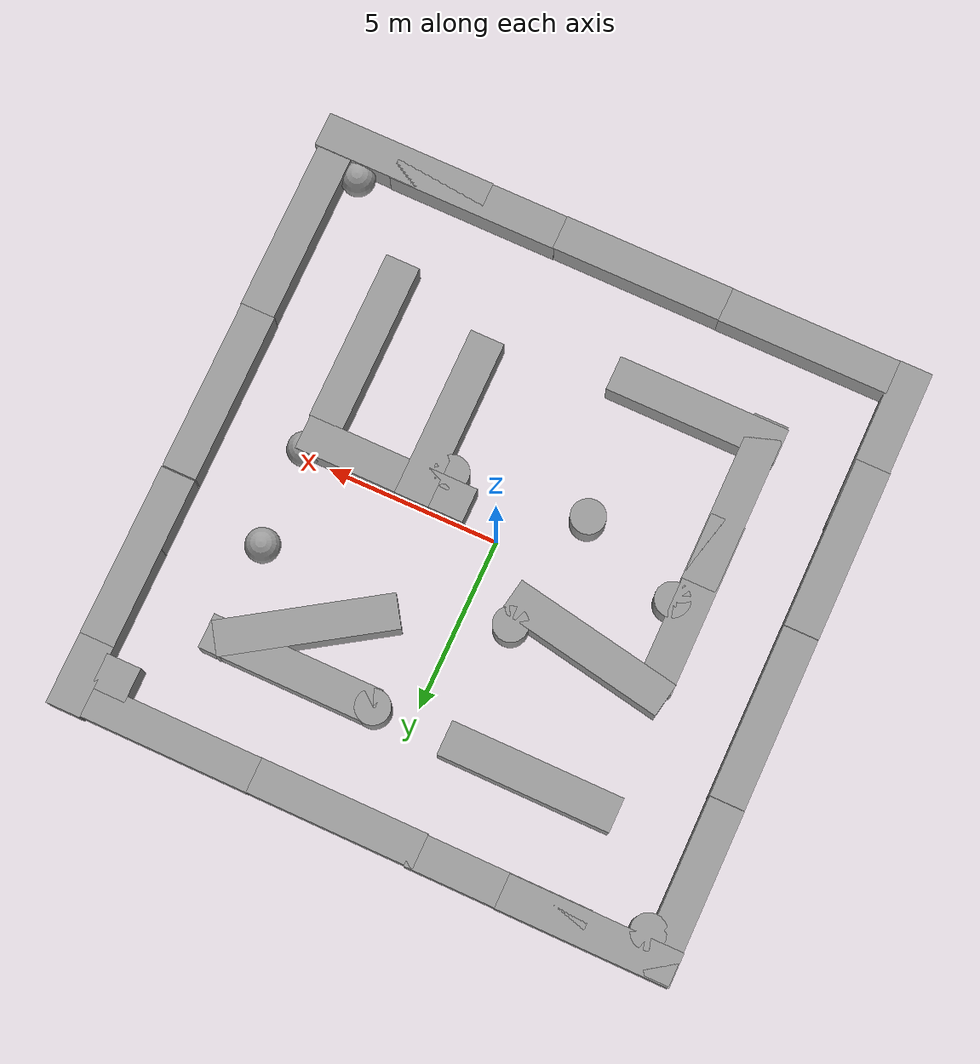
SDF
<?xml version='1.0'?>
<sdf version='1.7'>
  <model name='turtlebot3_world'>
    <link name='turtlebot3_world::link_1'>
      <inertial>
        <mass>4.98343</mass>
        <inertia>
          <ixx>10.7287</ixx>
          <ixy>0</ixy>
          <ixz>0</ixz>
          <iyy>0.830571</iyy>
          <iyz>0</iyz>
          <izz>10.7287</izz>
        </inertia>
        <pose>0 0 0 0 -0 0</pose>
      </inertial>
      <pose>-8.50691 6.51028 0.5 0 -0 0</pose>
      <self_collide>0</self_collide>
      <enable_wind>0</enable_wind>
      <kinematic>0</kinematic>
      <visual name='visual'>
        <pose>0 0 0 0 -0 0</pose>
        <geometry>
          <box>
            <size>1 4.98342 1</size>
          </box>
        </geometry>
        <material>
          <lighting>1</lighting>
          <script>
            <uri>file://media/materials/scripts/gazebo.material</uri>
            <name>Gazebo/Grey</name>
          </script>
          <shader type='pixel'/>
        </material>
        <transparency>0</transparency>
        <cast_shadows>1</cast_shadows>
      </visual>
      <collision name='collision'>
        <laser_retro>0</laser_retro>
        <max_contacts>10</max_contacts>
        <pose>0 0 0 0 -0 0</pose>
        <geometry>
          <box>
            <size>1 4.98342 1</size>
          </box>
        </geometry>
        <surface>
          <friction>
            <ode>
              <mu>1</mu>
              <mu2>1</mu2>
              <fdir1>0 0 0</fdir1>
              <slip1>0</slip1>
              <slip2>0</slip2>
            </ode>
            <torsional>
              <coefficient>1</coefficient>
              <patch_radius>0</patch_radius>
              <surface_radius>0</surface_radius>
              <use_patch_radius>1</use_patch_radius>
              <ode>
                <slip>0</slip>
              </ode>
            </torsional>
          </friction>
          <bounce>
            <restitution_coefficient>0</restitution_coefficient>
            <threshold>1e+06</threshold>
          </bounce>
          <contact>
            <collide_without_contact>0</collide_without_contact>
            <collide_without_contact_bitmask>1</collide_without_contact_bitmask>
            <collide_bitmask>1</collide_bitmask>
            <ode>
              <soft_cfm>0</soft_cfm>
              <soft_erp>0.2</soft_erp>
              <kp>1e+13</kp>
              <kd>1</kd>
              <max_vel>0.01</max_vel>
              <min_depth>0</min_depth>
            </ode>
            <bullet>
              <split_impulse>1</split_impulse>
              <split_impulse_penetration_threshold>-0.01</split_impulse_penetration_threshold>
              <soft_cfm>0</soft_cfm>
              <soft_erp>0.2</soft_erp>
              <kp>1e+13</kp>
              <kd>1</kd>
            </bullet>
          </contact>
        </surface>
      </collision>
    </link>
    <link name='link_0'>
      <inertial>
        <mass>1</mass>
        <inertia>
          <ixx>0.145833</ixx>
          <ixy>0</ixy>
          <ixz>0</ixz>
          <iyy>0.145833</iyy>
          <iyz>0</iyz>
          <izz>0.125</izz>
        </inertia>
      </inertial>
      <pose>-2.04016 -1.52743 0.5 0 -0 0</pose>
      <self_collide>0</self_collide>
      <enable_wind>0</enable_wind>
      <kinematic>0</kinematic>
      <visual name='visual'>
        <pose>0 0 0 0 -0 0</pose>
        <geometry>
          <cylinder>
            <radius>0.5</radius>
            <length>1</length>
          </cylinder>
        </geometry>
        <material>
          <lighting>1</lighting>
          <script>
            <uri>file://media/materials/scripts/gazebo.material</uri>
            <name>Gazebo/Grey</name>
          </script>
          <shader type='pixel'/>
        </material>
        <transparency>0</transparency>
        <cast_shadows>1</cast_shadows>
      </visual>
      <collision name='collision'>
        <laser_retro>0</laser_retro>
        <max_contacts>10</max_contacts>
        <pose>0 0 0 0 -0 0</pose>
        <geometry>
          <cylinder>
            <radius>0.5</radius>
            <length>1</length>
          </cylinder>
        </geometry>
        <surface>
          <friction>
            <ode>
              <mu>1</mu>
              <mu2>1</mu2>
              <fdir1>0 0 0</fdir1>
              <slip1>0</slip1>
              <slip2>0</slip2>
            </ode>
            <torsional>
              <coefficient>1</coefficient>
              <patch_radius>0</patch_radius>
              <surface_radius>0</surface_radius>
              <use_patch_radius>1</use_patch_radius>
              <ode>
                <slip>0</slip>
              </ode>
            </torsional>
          </friction>
          <bounce>
            <restitution_coefficient>0</restitution_coefficient>
            <threshold>1e+06</threshold>
          </bounce>
          <contact>
            <collide_without_contact>0</collide_without_contact>
            <collide_without_contact_bitmask>1</collide_without_contact_bitmask>
            <collide_bitmask>1</collide_bitmask>
            <ode>
              <soft_cfm>0</soft_cfm>
              <soft_erp>0.2</soft_erp>
              <kp>1e+13</kp>
              <kd>1</kd>
              <max_vel>0.01</max_vel>
              <min_depth>0</min_depth>
            </ode>
            <bullet>
              <split_impulse>1</split_impulse>
              <split_impulse_penetration_threshold>-0.01</split_impulse_penetration_threshold>
              <soft_cfm>0</soft_cfm>
              <soft_erp>0.2</soft_erp>
              <kp>1e+13</kp>
              <kd>1</kd>
            </bullet>
          </contact>
        </surface>
      </collision>
    </link>
    <link name='link_1'>
      <inertial>
        <mass>1</mass>
        <inertia>
          <ixx>0.145833</ixx>
          <ixy>0</ixy>
          <ixz>0</ixz>
          <iyy>0.145833</iyy>
          <iyz>0</iyz>
          <izz>0.125</izz>
        </inertia>
      </inertial>
      <pose>-1.34414 2.00991 0.5 0 -0 0</pose>
      <self_collide>0</self_collide>
      <enable_wind>0</enable_wind>
      <kinematic>0</kinematic>
      <visual name='visual'>
        <pose>0 0 0 0 -0 0</pose>
        <geometry>
          <cylinder>
            <radius>0.5</radius>
            <length>1</length>
          </cylinder>
        </geometry>
        <material>
          <lighting>1</lighting>
          <script>
            <uri>file://media/materials/scripts/gazebo.material</uri>
            <name>Gazebo/Grey</name>
          </script>
          <shader type='pixel'/>
        </material>
        <transparency>0</transparency>
        <cast_shadows>1</cast_shadows>
      </visual>
      <collision name='collision'>
        <laser_retro>0</laser_retro>
        <max_contacts>10</max_contacts>
        <pose>0 0 0 0 -0 0</pose>
        <geometry>
          <cylinder>
            <radius>0.5</radius>
            <length>1</length>
          </cylinder>
        </geometry>
        <surface>
          <friction>
            <ode>
              <mu>1</mu>
              <mu2>1</mu2>
              <fdir1>0 0 0</fdir1>
              <slip1>0</slip1>
              <slip2>0</slip2>
            </ode>
            <torsional>
              <coefficient>1</coefficient>
              <patch_radius>0</patch_radius>
              <surface_radius>0</surface_radius>
              <use_patch_radius>1</use_patch_radius>
              <ode>
                <slip>0</slip>
              </ode>
            </torsional>
          </friction>
          <bounce>
            <restitution_coefficient>0</restitution_coefficient>
            <threshold>1e+06</threshold>
          </bounce>
          <contact>
            <collide_without_contact>0</collide_without_contact>
            <collide_without_contact_bitmask>1</collide_without_contact_bitmask>
            <collide_bitmask>1</collide_bitmask>
            <ode>
              <soft_cfm>0</soft_cfm>
              <soft_erp>0.2</soft_erp>
              <kp>1e+13</kp>
              <kd>1</kd>
              <max_vel>0.01</max_vel>
              <min_depth>0</min_depth>
            </ode>
            <bullet>
              <split_impulse>1</split_impulse>
              <split_impulse_penetration_threshold>-0.01</split_impulse_penetration_threshold>
              <soft_cfm>0</soft_cfm>
              <soft_erp>0.2</soft_erp>
              <kp>1e+13</kp>
              <kd>1</kd>
            </bullet>
          </contact>
        </surface>
      </collision>
    </link>
    <link name='link_11'>
      <inertial>
        <mass>1</mass>
        <inertia>
          <ixx>0.1</ixx>
          <ixy>0</ixy>
          <ixz>0</ixz>
          <iyy>0.1</iyy>
          <iyz>0</iyz>
          <izz>0.1</izz>
        </inertia>
      </inertial>
      <pose>5.68871 2.74628 0.5 0 -0 0</pose>
      <self_collide>0</self_collide>
      <enable_wind>0</enable_wind>
      <kinematic>0</kinematic>
      <visual name='visual'>
        <pose>0 0 0 0 -0 0</pose>
        <geometry>
          <sphere>
            <radius>0.5</radius>
          </sphere>
        </geometry>
        <material>
          <lighting>1</lighting>
          <script>
            <uri>file://media/materials/scripts/gazebo.material</uri>
            <name>Gazebo/Grey</name>
          </script>
          <shader type='pixel'/>
        </material>
        <transparency>0</transparency>
        <cast_shadows>1</cast_shadows>
      </visual>
      <collision name='collision'>
        <laser_retro>0</laser_retro>
        <max_contacts>10</max_contacts>
        <pose>0 0 0 0 -0 0</pose>
        <geometry>
          <sphere>
            <radius>0.5</radius>
          </sphere>
        </geometry>
        <surface>
          <friction>
            <ode>
              <mu>1</mu>
              <mu2>1</mu2>
              <fdir1>0 0 0</fdir1>
              <slip1>0</slip1>
              <slip2>0</slip2>
            </ode>
            <torsional>
              <coefficient>1</coefficient>
              <patch_radius>0</patch_radius>
              <surface_radius>0</surface_radius>
              <use_patch_radius>1</use_patch_radius>
              <ode>
                <slip>0</slip>
              </ode>
            </torsional>
          </friction>
          <bounce>
            <restitution_coefficient>0</restitution_coefficient>
            <threshold>1e+06</threshold>
          </bounce>
          <contact>
            <collide_without_contact>0</collide_without_contact>
            <collide_without_contact_bitmask>1</collide_without_contact_bitmask>
            <collide_bitmask>1</collide_bitmask>
            <ode>
              <soft_cfm>0</soft_cfm>
              <soft_erp>0.2</soft_erp>
              <kp>1e+13</kp>
              <kd>1</kd>
              <max_vel>0.01</max_vel>
              <min_depth>0</min_depth>
            </ode>
            <bullet>
              <split_impulse>1</split_impulse>
              <split_impulse_penetration_threshold>-0.01</split_impulse_penetration_threshold>
              <soft_cfm>0</soft_cfm>
              <soft_erp>0.2</soft_erp>
              <kp>1e+13</kp>
              <kd>1</kd>
            </bullet>
          </contact>
        </surface>
      </collision>
    </link>
    <link name='link_2'>
      <inertial>
        <mass>1</mass>
        <inertia>
          <ixx>0.145833</ixx>
          <ixy>0</ixy>
          <ixz>0</ixz>
          <iyy>0.145833</iyy>
          <iyz>0</iyz>
          <izz>0.125</izz>
        </inertia>
      </inertial>
      <pose>1.07519 5.54576 0.5 0 -0 0</pose>
      <self_collide>0</self_collide>
      <enable_wind>0</enable_wind>
      <kinematic>0</kinematic>
      <visual name='visual'>
        <pose>0 0 0 0 -0 0</pose>
        <geometry>
          <cylinder>
            <radius>0.5</radius>
            <length>1</length>
          </cylinder>
        </geometry>
        <material>
          <lighting>1</lighting>
          <script>
            <uri>file://media/materials/scripts/gazebo.material</uri>
            <name>Gazebo/Grey</name>
          </script>
          <shader type='pixel'/>
        </material>
        <transparency>0</transparency>
        <cast_shadows>1</cast_shadows>
      </visual>
      <collision name='collision'>
        <laser_retro>0</laser_retro>
        <max_contacts>10</max_contacts>
        <pose>0 0 0 0 -0 0</pose>
        <geometry>
          <cylinder>
            <radius>0.5</radius>
            <length>1</length>
          </cylinder>
        </geometry>
        <surface>
          <friction>
            <ode>
              <mu>1</mu>
              <mu2>1</mu2>
              <fdir1>0 0 0</fdir1>
              <slip1>0</slip1>
              <slip2>0</slip2>
            </ode>
            <torsional>
              <coefficient>1</coefficient>
              <patch_radius>0</patch_radius>
              <surface_radius>0</surface_radius>
              <use_patch_radius>1</use_patch_radius>
              <ode>
                <slip>0</slip>
              </ode>
            </torsional>
          </friction>
          <bounce>
            <restitution_coefficient>0</restitution_coefficient>
            <threshold>1e+06</threshold>
          </bounce>
          <contact>
            <collide_without_contact>0</collide_without_contact>
            <collide_without_contact_bitmask>1</collide_without_contact_bitmask>
            <collide_bitmask>1</collide_bitmask>
            <ode>
              <soft_cfm>0</soft_cfm>
              <soft_erp>0.2</soft_erp>
              <kp>1e+13</kp>
              <kd>1</kd>
              <max_vel>0.01</max_vel>
              <min_depth>0</min_depth>
            </ode>
            <bullet>
              <split_impulse>1</split_impulse>
              <split_impulse_penetration_threshold>-0.01</split_impulse_penetration_threshold>
              <soft_cfm>0</soft_cfm>
              <soft_erp>0.2</soft_erp>
              <kp>1e+13</kp>
              <kd>1</kd>
            </bullet>
          </contact>
        </surface>
      </collision>
    </link>
    <link name='link_3'>
      <inertial>
        <mass>1</mass>
        <inertia>
          <ixx>0.145833</ixx>
          <ixy>0</ixy>
          <ixz>0</ixz>
          <iyy>0.145833</iyy>
          <iyz>0</iyz>
          <izz>0.125</izz>
        </inertia>
      </inertial>
      <pose>1.81796 -1.11314 0.5 0 -0 0</pose>
      <self_collide>0</self_collide>
      <enable_wind>0</enable_wind>
      <kinematic>0</kinematic>
      <visual name='visual'>
        <pose>0 0 0 0 -0 0</pose>
        <geometry>
          <cylinder>
            <radius>0.5</radius>
            <length>1</length>
          </cylinder>
        </geometry>
        <material>
          <lighting>1</lighting>
          <script>
            <uri>file://media/materials/scripts/gazebo.material</uri>
            <name>Gazebo/Grey</name>
          </script>
          <shader type='pixel'/>
        </material>
        <transparency>0</transparency>
        <cast_shadows>1</cast_shadows>
      </visual>
      <collision name='collision'>
        <laser_retro>0</laser_retro>
        <max_contacts>10</max_contacts>
        <pose>0 0 0 0 -0 0</pose>
        <geometry>
          <cylinder>
            <radius>0.5</radius>
            <length>1</length>
          </cylinder>
        </geometry>
        <surface>
          <friction>
            <ode>
              <mu>1</mu>
              <mu2>1</mu2>
              <fdir1>0 0 0</fdir1>
              <slip1>0</slip1>
              <slip2>0</slip2>
            </ode>
            <torsional>
              <coefficient>1</coefficient>
              <patch_radius>0</patch_radius>
              <surface_radius>0</surface_radius>
              <use_patch_radius>1</use_patch_radius>
              <ode>
                <slip>0</slip>
              </ode>
            </torsional>
          </friction>
          <bounce>
            <restitution_coefficient>0</restitution_coefficient>
            <threshold>1e+06</threshold>
          </bounce>
          <contact>
            <collide_without_contact>0</collide_without_contact>
            <collide_without_contact_bitmask>1</collide_without_contact_bitmask>
            <collide_bitmask>1</collide_bitmask>
            <ode>
              <soft_cfm>0</soft_cfm>
              <soft_erp>0.2</soft_erp>
              <kp>1e+13</kp>
              <kd>1</kd>
              <max_vel>0.01</max_vel>
              <min_depth>0</min_depth>
            </ode>
            <bullet>
              <split_impulse>1</split_impulse>
              <split_impulse_penetration_threshold>-0.01</split_impulse_penetration_threshold>
              <soft_cfm>0</soft_cfm>
              <soft_erp>0.2</soft_erp>
              <kp>1e+13</kp>
              <kd>1</kd>
            </bullet>
          </contact>
        </surface>
      </collision>
    </link>
    <link name='link_4'>
      <inertial>
        <mass>1</mass>
        <inertia>
          <ixx>0.1</ixx>
          <ixy>0</ixy>
          <ixz>0</ixz>
          <iyy>0.1</iyy>
          <iyz>0</iyz>
          <izz>0.1</izz>
        </inertia>
      </inertial>
      <pose>5.79355 -0.136695 0.5 0 -0 0</pose>
      <self_collide>0</self_collide>
      <enable_wind>0</enable_wind>
      <kinematic>0</kinematic>
      <visual name='visual'>
        <pose>0 0 0 0 -0 0</pose>
        <geometry>
          <sphere>
            <radius>0.5</radius>
          </sphere>
        </geometry>
        <material>
          <lighting>1</lighting>
          <script>
            <uri>file://media/materials/scripts/gazebo.material</uri>
            <name>Gazebo/Grey</name>
          </script>
          <shader type='pixel'/>
        </material>
        <transparency>0</transparency>
        <cast_shadows>1</cast_shadows>
      </visual>
      <collision name='collision'>
        <laser_retro>0</laser_retro>
        <max_contacts>10</max_contacts>
        <pose>0 0 0 0 -0 0</pose>
        <geometry>
          <sphere>
            <radius>0.5</radius>
          </sphere>
        </geometry>
        <surface>
          <friction>
            <ode>
              <mu>1</mu>
              <mu2>1</mu2>
              <fdir1>0 0 0</fdir1>
              <slip1>0</slip1>
              <slip2>0</slip2>
            </ode>
            <torsional>
              <coefficient>1</coefficient>
              <patch_radius>0</patch_radius>
              <surface_radius>0</surface_radius>
              <use_patch_radius>1</use_patch_radius>
              <ode>
                <slip>0</slip>
              </ode>
            </torsional>
          </friction>
          <bounce>
            <restitution_coefficient>0</restitution_coefficient>
            <threshold>1e+06</threshold>
          </bounce>
          <contact>
            <collide_without_contact>0</collide_without_contact>
            <collide_without_contact_bitmask>1</collide_without_contact_bitmask>
            <collide_bitmask>1</collide_bitmask>
            <ode>
              <soft_cfm>0</soft_cfm>
              <soft_erp>0.2</soft_erp>
              <kp>1e+13</kp>
              <kd>1</kd>
              <max_vel>0.01</max_vel>
              <min_depth>0</min_depth>
            </ode>
            <bullet>
              <split_impulse>1</split_impulse>
              <split_impulse_penetration_threshold>-0.01</split_impulse_penetration_threshold>
              <soft_cfm>0</soft_cfm>
              <soft_erp>0.2</soft_erp>
              <kp>1e+13</kp>
              <kd>1</kd>
            </bullet>
          </contact>
        </surface>
      </collision>
    </link>
    <link name='link_5'>
      <inertial>
        <mass>1</mass>
        <inertia>
          <ixx>0.1</ixx>
          <ixy>0</ixy>
          <ixz>0</ixz>
          <iyy>0.1</iyy>
          <iyz>0</iyz>
          <izz>0.1</izz>
        </inertia>
      </inertial>
      <pose>7.73155 -7.74781 0.5 0 -0 0</pose>
      <self_collide>0</self_collide>
      <enable_wind>0</enable_wind>
      <kinematic>0</kinematic>
      <visual name='visual'>
        <pose>0 0 0 0 -0 0</pose>
        <geometry>
          <sphere>
            <radius>0.5</radius>
          </sphere>
        </geometry>
        <material>
          <lighting>1</lighting>
          <script>
            <uri>file://media/materials/scripts/gazebo.material</uri>
            <name>Gazebo/Grey</name>
          </script>
          <shader type='pixel'/>
        </material>
        <transparency>0</transparency>
        <cast_shadows>1</cast_shadows>
      </visual>
      <collision name='collision'>
        <laser_retro>0</laser_retro>
        <max_contacts>10</max_contacts>
        <pose>0 0 0 0 -0 0</pose>
        <geometry>
          <sphere>
            <radius>0.5</radius>
          </sphere>
        </geometry>
        <surface>
          <friction>
            <ode>
              <mu>1</mu>
              <mu2>1</mu2>
              <fdir1>0 0 0</fdir1>
              <slip1>0</slip1>
              <slip2>0</slip2>
            </ode>
            <torsional>
              <coefficient>1</coefficient>
              <patch_radius>0</patch_radius>
              <surface_radius>0</surface_radius>
              <use_patch_radius>1</use_patch_radius>
              <ode>
                <slip>0</slip>
              </ode>
            </torsional>
          </friction>
          <bounce>
            <restitution_coefficient>0</restitution_coefficient>
            <threshold>1e+06</threshold>
          </bounce>
          <contact>
            <collide_without_contact>0</collide_without_contact>
            <collide_without_contact_bitmask>1</collide_without_contact_bitmask>
            <collide_bitmask>1</collide_bitmask>
            <ode>
              <soft_cfm>0</soft_cfm>
              <soft_erp>0.2</soft_erp>
              <kp>1e+13</kp>
              <kd>1</kd>
              <max_vel>0.01</max_vel>
              <min_depth>0</min_depth>
            </ode>
            <bullet>
              <split_impulse>1</split_impulse>
              <split_impulse_penetration_threshold>-0.01</split_impulse_penetration_threshold>
              <soft_cfm>0</soft_cfm>
              <soft_erp>0.2</soft_erp>
              <kp>1e+13</kp>
              <kd>1</kd>
            </bullet>
          </contact>
        </surface>
      </collision>
    </link>
    <link name='link_6'>
      <inertial>
        <mass>1</mass>
        <inertia>
          <ixx>0.166667</ixx>
          <ixy>0</ixy>
          <ixz>0</ixz>
          <iyy>0.166667</iyy>
          <iyz>0</iyz>
          <izz>0.166667</izz>
        </inertia>
      </inertial>
      <pose>7.62115 7.66766 0.5 0 -0 0</pose>
      <self_collide>0</self_collide>
      <enable_wind>0</enable_wind>
      <kinematic>0</kinematic>
      <visual name='visual'>
        <pose>0 0 0 0 -0 0</pose>
        <geometry>
          <box>
            <size>1 1 1</size>
          </box>
        </geometry>
        <material>
          <lighting>1</lighting>
          <script>
            <uri>file://media/materials/scripts/gazebo.material</uri>
            <name>Gazebo/Grey</name>
          </script>
          <shader type='pixel'/>
        </material>
        <transparency>0</transparency>
        <cast_shadows>1</cast_shadows>
      </visual>
      <collision name='collision'>
        <laser_retro>0</laser_retro>
        <max_contacts>10</max_contacts>
        <pose>0 0 0 0 -0 0</pose>
        <geometry>
          <box>
            <size>1 1 1</size>
          </box>
        </geometry>
        <surface>
          <friction>
            <ode>
              <mu>1</mu>
              <mu2>1</mu2>
              <fdir1>0 0 0</fdir1>
              <slip1>0</slip1>
              <slip2>0</slip2>
            </ode>
            <torsional>
              <coefficient>1</coefficient>
              <patch_radius>0</patch_radius>
              <surface_radius>0</surface_radius>
              <use_patch_radius>1</use_patch_radius>
              <ode>
                <slip>0</slip>
              </ode>
            </torsional>
          </friction>
          <bounce>
            <restitution_coefficient>0</restitution_coefficient>
            <threshold>1e+06</threshold>
          </bounce>
          <contact>
            <collide_without_contact>0</collide_without_contact>
            <collide_without_contact_bitmask>1</collide_without_contact_bitmask>
            <collide_bitmask>1</collide_bitmask>
            <ode>
              <soft_cfm>0</soft_cfm>
              <soft_erp>0.2</soft_erp>
              <kp>1e+13</kp>
              <kd>1</kd>
              <max_vel>0.01</max_vel>
              <min_depth>0</min_depth>
            </ode>
            <bullet>
              <split_impulse>1</split_impulse>
              <split_impulse_penetration_threshold>-0.01</split_impulse_penetration_threshold>
              <soft_cfm>0</soft_cfm>
              <soft_erp>0.2</soft_erp>
              <kp>1e+13</kp>
              <kd>1</kd>
            </bullet>
          </contact>
        </surface>
      </collision>
    </link>
    <link name='link_7'>
      <inertial>
        <mass>1</mass>
        <inertia>
          <ixx>0.145833</ixx>
          <ixy>0</ixy>
          <ixz>0</ixz>
          <iyy>0.145833</iyy>
          <iyz>0</iyz>
          <izz>0.125</izz>
        </inertia>
      </inertial>
      <pose>-7.96406 7.91542 0.5 0 -0 0</pose>
      <self_collide>0</self_collide>
      <enable_wind>0</enable_wind>
      <kinematic>0</kinematic>
      <visual name='visual'>
        <pose>0 0 0 0 -0 0</pose>
        <geometry>
          <cylinder>
            <radius>0.5</radius>
            <length>1</length>
          </cylinder>
        </geometry>
        <material>
          <lighting>1</lighting>
          <script>
            <uri>file://media/materials/scripts/gazebo.material</uri>
            <name>Gazebo/Grey</name>
          </script>
          <shader type='pixel'/>
        </material>
        <transparency>0</transparency>
        <cast_shadows>1</cast_shadows>
      </visual>
      <collision name='collision'>
        <laser_retro>0</laser_retro>
        <max_contacts>10</max_contacts>
        <pose>0 0 0 0 -0 0</pose>
        <geometry>
          <cylinder>
            <radius>0.5</radius>
            <length>1</length>
          </cylinder>
        </geometry>
        <surface>
          <friction>
            <ode>
              <mu>1</mu>
              <mu2>1</mu2>
              <fdir1>0 0 0</fdir1>
              <slip1>0</slip1>
              <slip2>0</slip2>
            </ode>
            <torsional>
              <coefficient>1</coefficient>
              <patch_radius>0</patch_radius>
              <surface_radius>0</surface_radius>
              <use_patch_radius>1</use_patch_radius>
              <ode>
                <slip>0</slip>
              </ode>
            </torsional>
          </friction>
          <bounce>
            <restitution_coefficient>0</restitution_coefficient>
            <threshold>1e+06</threshold>
          </bounce>
          <contact>
            <collide_without_contact>0</collide_without_contact>
            <collide_without_contact_bitmask>1</collide_without_contact_bitmask>
            <collide_bitmask>1</collide_bitmask>
            <ode>
              <soft_cfm>0</soft_cfm>
              <soft_erp>0.2</soft_erp>
              <kp>1e+13</kp>
              <kd>1</kd>
              <max_vel>0.01</max_vel>
              <min_depth>0</min_depth>
            </ode>
            <bullet>
              <split_impulse>1</split_impulse>
              <split_impulse_penetration_threshold>-0.01</split_impulse_penetration_threshold>
              <soft_cfm>0</soft_cfm>
              <soft_erp>0.2</soft_erp>
              <kp>1e+13</kp>
              <kd>1</kd>
            </bullet>
          </contact>
        </surface>
      </collision>
    </link>
    <link name='link_8'>
      <inertial>
        <mass>1</mass>
        <inertia>
          <ixx>0.145833</ixx>
          <ixy>0</ixy>
          <ixz>0</ixz>
          <iyy>0.145833</iyy>
          <iyz>0</iyz>
          <izz>0.125</izz>
        </inertia>
      </inertial>
      <pose>-5.01755 -0.384631 0.5 0 -0 0</pose>
      <self_collide>0</self_collide>
      <enable_wind>0</enable_wind>
      <kinematic>0</kinematic>
      <visual name='visual'>
        <pose>0 0 0 0 -0 0</pose>
        <geometry>
          <cylinder>
            <radius>0.5</radius>
            <length>1</length>
          </cylinder>
        </geometry>
        <material>
          <lighting>1</lighting>
          <script>
            <uri>file://media/materials/scripts/gazebo.material</uri>
            <name>Gazebo/Grey</name>
          </script>
          <shader type='pixel'/>
        </material>
        <transparency>0</transparency>
        <cast_shadows>1</cast_shadows>
      </visual>
      <collision name='collision'>
        <laser_retro>0</laser_retro>
        <max_contacts>10</max_contacts>
        <pose>0 0 0 0 -0 0</pose>
        <geometry>
          <cylinder>
            <radius>0.5</radius>
            <length>1</length>
          </cylinder>
        </geometry>
        <surface>
          <friction>
            <ode>
              <mu>1</mu>
              <mu2>1</mu2>
              <fdir1>0 0 0</fdir1>
              <slip1>0</slip1>
              <slip2>0</slip2>
            </ode>
            <torsional>
              <coefficient>1</coefficient>
              <patch_radius>0</patch_radius>
              <surface_radius>0</surface_radius>
              <use_patch_radius>1</use_patch_radius>
              <ode>
                <slip>0</slip>
              </ode>
            </torsional>
          </friction>
          <bounce>
            <restitution_coefficient>0</restitution_coefficient>
            <threshold>1e+06</threshold>
          </bounce>
          <contact>
            <collide_without_contact>0</collide_without_contact>
            <collide_without_contact_bitmask>1</collide_without_contact_bitmask>
            <collide_bitmask>1</collide_bitmask>
            <ode>
              <soft_cfm>0</soft_cfm>
              <soft_erp>0.2</soft_erp>
              <kp>1e+13</kp>
              <kd>1</kd>
              <max_vel>0.01</max_vel>
              <min_depth>0</min_depth>
            </ode>
            <bullet>
              <split_impulse>1</split_impulse>
              <split_impulse_penetration_threshold>-0.01</split_impulse_penetration_threshold>
              <soft_cfm>0</soft_cfm>
              <soft_erp>0.2</soft_erp>
              <kp>1e+13</kp>
              <kd>1</kd>
            </bullet>
          </contact>
        </surface>
      </collision>
    </link>
    <link name='turtlebot3_world::link_1_clone'>
      <inertial>
        <mass>4.98343</mass>
        <inertia>
          <ixx>10.7287</ixx>
          <ixy>0</ixy>
          <ixz>0</ixz>
          <iyy>0.830571</iyy>
          <iyz>0</iyz>
          <izz>10.7287</izz>
        </inertia>
        <pose>0 0 0 0 -0 0</pose>
      </inertial>
      <pose>-8.49911 1.51651 0.5 0 -0 0</pose>
      <self_collide>0</self_collide>
      <enable_wind>0</enable_wind>
      <kinematic>0</kinematic>
      <visual name='visual'>
        <pose>0 0 0 0 -0 0</pose>
        <geometry>
          <box>
            <size>1 4.98342 1</size>
          </box>
        </geometry>
        <material>
          <lighting>1</lighting>
          <script>
            <uri>file://media/materials/scripts/gazebo.material</uri>
            <name>Gazebo/Grey</name>
          </script>
          <shader type='pixel'/>
        </material>
        <transparency>0</transparency>
        <cast_shadows>1</cast_shadows>
      </visual>
      <collision name='collision'>
        <laser_retro>0</laser_retro>
        <max_contacts>10</max_contacts>
        <pose>0 0 0 0 -0 0</pose>
        <geometry>
          <box>
            <size>1 4.98342 1</size>
          </box>
        </geometry>
        <surface>
          <friction>
            <ode>
              <mu>1</mu>
              <mu2>1</mu2>
              <fdir1>0 0 0</fdir1>
              <slip1>0</slip1>
              <slip2>0</slip2>
            </ode>
            <torsional>
              <coefficient>1</coefficient>
              <patch_radius>0</patch_radius>
              <surface_radius>0</surface_radius>
              <use_patch_radius>1</use_patch_radius>
              <ode>
                <slip>0</slip>
              </ode>
            </torsional>
          </friction>
          <bounce>
            <restitution_coefficient>0</restitution_coefficient>
            <threshold>1e+06</threshold>
          </bounce>
          <contact>
            <collide_without_contact>0</collide_without_contact>
            <collide_without_contact_bitmask>1</collide_without_contact_bitmask>
            <collide_bitmask>1</collide_bitmask>
            <ode>
              <soft_cfm>0</soft_cfm>
              <soft_erp>0.2</soft_erp>
              <kp>1e+13</kp>
              <kd>1</kd>
              <max_vel>0.01</max_vel>
              <min_depth>0</min_depth>
            </ode>
            <bullet>
              <split_impulse>1</split_impulse>
              <split_impulse_penetration_threshold>-0.01</split_impulse_penetration_threshold>
              <soft_cfm>0</soft_cfm>
              <soft_erp>0.2</soft_erp>
              <kp>1e+13</kp>
              <kd>1</kd>
            </bullet>
          </contact>
        </surface>
      </collision>
    </link>
    <link name='turtlebot3_world::link_1_clone_0'>
      <inertial>
        <mass>4.98343</mass>
        <inertia>
          <ixx>10.7287</ixx>
          <ixy>0</ixy>
          <ixz>0</ixz>
          <iyy>0.830571</iyy>
          <iyz>0</iyz>
          <izz>10.7287</izz>
        </inertia>
        <pose>0 0 0 0 -0 0</pose>
      </inertial>
      <pose>-8.5021 -3.47749 0.5 0 -0 0</pose>
      <self_collide>0</self_collide>
      <enable_wind>0</enable_wind>
      <kinematic>0</kinematic>
      <visual name='visual'>
        <pose>0 0 0 0 -0 0</pose>
        <geometry>
          <box>
            <size>1 4.98342 1</size>
          </box>
        </geometry>
        <material>
          <lighting>1</lighting>
          <script>
            <uri>file://media/materials/scripts/gazebo.material</uri>
            <name>Gazebo/Grey</name>
          </script>
          <shader type='pixel'/>
        </material>
        <transparency>0</transparency>
        <cast_shadows>1</cast_shadows>
      </visual>
      <collision name='collision'>
        <laser_retro>0</laser_retro>
        <max_contacts>10</max_contacts>
        <pose>0 0 0 0 -0 0</pose>
        <geometry>
          <box>
            <size>1 4.98342 1</size>
          </box>
        </geometry>
        <surface>
          <friction>
            <ode>
              <mu>1</mu>
              <mu2>1</mu2>
              <fdir1>0 0 0</fdir1>
              <slip1>0</slip1>
              <slip2>0</slip2>
            </ode>
            <torsional>
              <coefficient>1</coefficient>
              <patch_radius>0</patch_radius>
              <surface_radius>0</surface_radius>
              <use_patch_radius>1</use_patch_radius>
              <ode>
                <slip>0</slip>
              </ode>
            </torsional>
          </friction>
          <bounce>
            <restitution_coefficient>0</restitution_coefficient>
            <threshold>1e+06</threshold>
          </bounce>
          <contact>
            <collide_without_contact>0</collide_without_contact>
            <collide_without_contact_bitmask>1</collide_without_contact_bitmask>
            <collide_bitmask>1</collide_bitmask>
            <ode>
              <soft_cfm>0</soft_cfm>
              <soft_erp>0.2</soft_erp>
              <kp>1e+13</kp>
              <kd>1</kd>
              <max_vel>0.01</max_vel>
              <min_depth>0</min_depth>
            </ode>
            <bullet>
              <split_impulse>1</split_impulse>
              <split_impulse_penetration_threshold>-0.01</split_impulse_penetration_threshold>
              <soft_cfm>0</soft_cfm>
              <soft_erp>0.2</soft_erp>
              <kp>1e+13</kp>
              <kd>1</kd>
            </bullet>
          </contact>
        </surface>
      </collision>
    </link>
    <link name='turtlebot3_world::link_1_clone_1'>
      <inertial>
        <mass>4.98343</mass>
        <inertia>
          <ixx>10.7287</ixx>
          <ixy>0</ixy>
          <ixz>0</ixz>
          <iyy>0.830571</iyy>
          <iyz>0</iyz>
          <izz>10.7287</izz>
        </inertia>
        <pose>0 0 0 0 -0 0</pose>
      </inertial>
      <pose>-8.48256 -6.51074 0.5 0 -0 0</pose>
      <self_collide>0</self_collide>
      <enable_wind>0</enable_wind>
      <kinematic>0</kinematic>
      <visual name='visual'>
        <pose>0 0 0 0 -0 0</pose>
        <geometry>
          <box>
            <size>1 4.98342 1</size>
          </box>
        </geometry>
        <material>
          <lighting>1</lighting>
          <script>
            <uri>file://media/materials/scripts/gazebo.material</uri>
            <name>Gazebo/Grey</name>
          </script>
          <shader type='pixel'/>
        </material>
        <transparency>0</transparency>
        <cast_shadows>1</cast_shadows>
      </visual>
      <collision name='collision'>
        <laser_retro>0</laser_retro>
        <max_contacts>10</max_contacts>
        <pose>0 0 0 0 -0 0</pose>
        <geometry>
          <box>
            <size>1 4.98342 1</size>
          </box>
        </geometry>
        <surface>
          <friction>
            <ode>
              <mu>1</mu>
              <mu2>1</mu2>
              <fdir1>0 0 0</fdir1>
              <slip1>0</slip1>
              <slip2>0</slip2>
            </ode>
            <torsional>
              <coefficient>1</coefficient>
              <patch_radius>0</patch_radius>
              <surface_radius>0</surface_radius>
              <use_patch_radius>1</use_patch_radius>
              <ode>
                <slip>0</slip>
              </ode>
            </torsional>
          </friction>
          <bounce>
            <restitution_coefficient>0</restitution_coefficient>
            <threshold>1e+06</threshold>
          </bounce>
          <contact>
            <collide_without_contact>0</collide_without_contact>
            <collide_without_contact_bitmask>1</collide_without_contact_bitmask>
            <collide_bitmask>1</collide_bitmask>
            <ode>
              <soft_cfm>0</soft_cfm>
              <soft_erp>0.2</soft_erp>
              <kp>1e+13</kp>
              <kd>1</kd>
              <max_vel>0.01</max_vel>
              <min_depth>0</min_depth>
            </ode>
            <bullet>
              <split_impulse>1</split_impulse>
              <split_impulse_penetration_threshold>-0.01</split_impulse_penetration_threshold>
              <soft_cfm>0</soft_cfm>
              <soft_erp>0.2</soft_erp>
              <kp>1e+13</kp>
              <kd>1</kd>
            </bullet>
          </contact>
        </surface>
      </collision>
    </link>
    <link name='turtlebot3_world::link_1_clone_1_clone'>
      <inertial>
        <mass>4.98343</mass>
        <inertia>
          <ixx>10.7287</ixx>
          <ixy>0</ixy>
          <ixz>0</ixz>
          <iyy>0.830571</iyy>
          <iyz>0</iyz>
          <izz>10.7287</izz>
        </inertia>
        <pose>0 0 0 0 -0 0</pose>
      </inertial>
      <pose>8.55507 -5.5221 0.5 0 -0 0</pose>
      <self_collide>0</self_collide>
      <enable_wind>0</enable_wind>
      <kinematic>0</kinematic>
      <visual name='visual'>
        <pose>0 0 0 0 -0 0</pose>
        <geometry>
          <box>
            <size>1 4.98342 1</size>
          </box>
        </geometry>
        <material>
          <lighting>1</lighting>
          <script>
            <uri>file://media/materials/scripts/gazebo.material</uri>
            <name>Gazebo/Grey</name>
          </script>
          <shader type='pixel'/>
        </material>
        <transparency>0</transparency>
        <cast_shadows>1</cast_shadows>
      </visual>
      <collision name='collision'>
        <laser_retro>0</laser_retro>
        <max_contacts>10</max_contacts>
        <pose>0 0 0 0 -0 0</pose>
        <geometry>
          <box>
            <size>1 4.98342 1</size>
          </box>
        </geometry>
        <surface>
          <friction>
            <ode>
              <mu>1</mu>
              <mu2>1</mu2>
              <fdir1>0 0 0</fdir1>
              <slip1>0</slip1>
              <slip2>0</slip2>
            </ode>
            <torsional>
              <coefficient>1</coefficient>
              <patch_radius>0</patch_radius>
              <surface_radius>0</surface_radius>
              <use_patch_radius>1</use_patch_radius>
              <ode>
                <slip>0</slip>
              </ode>
            </torsional>
          </friction>
          <bounce>
            <restitution_coefficient>0</restitution_coefficient>
            <threshold>1e+06</threshold>
          </bounce>
          <contact>
            <collide_without_contact>0</collide_without_contact>
            <collide_without_contact_bitmask>1</collide_without_contact_bitmask>
            <collide_bitmask>1</collide_bitmask>
            <ode>
              <soft_cfm>0</soft_cfm>
              <soft_erp>0.2</soft_erp>
              <kp>1e+13</kp>
              <kd>1</kd>
              <max_vel>0.01</max_vel>
              <min_depth>0</min_depth>
            </ode>
            <bullet>
              <split_impulse>1</split_impulse>
              <split_impulse_penetration_threshold>-0.01</split_impulse_penetration_threshold>
              <soft_cfm>0</soft_cfm>
              <soft_erp>0.2</soft_erp>
              <kp>1e+13</kp>
              <kd>1</kd>
            </bullet>
          </contact>
        </surface>
      </collision>
    </link>
    <link name='turtlebot3_world::link_1_clone_1_clone_0'>
      <inertial>
        <mass>4.98343</mass>
        <inertia>
          <ixx>10.7287</ixx>
          <ixy>0</ixy>
          <ixz>0</ixz>
          <iyy>0.830571</iyy>
          <iyz>0</iyz>
          <izz>10.7287</izz>
        </inertia>
        <pose>0 0 0 0 -0 0</pose>
      </inertial>
      <pose>8.52926 -0.553425 0.5 0 -0 0</pose>
      <self_collide>0</self_collide>
      <enable_wind>0</enable_wind>
      <kinematic>0</kinematic>
      <visual name='visual'>
        <pose>0 0 0 0 -0 0</pose>
        <geometry>
          <box>
            <size>1 4.98342 1</size>
          </box>
        </geometry>
        <material>
          <lighting>1</lighting>
          <script>
            <uri>file://media/materials/scripts/gazebo.material</uri>
            <name>Gazebo/Grey</name>
          </script>
          <shader type='pixel'/>
        </material>
        <transparency>0</transparency>
        <cast_shadows>1</cast_shadows>
      </visual>
      <collision name='collision'>
        <laser_retro>0</laser_retro>
        <max_contacts>10</max_contacts>
        <pose>0 0 0 0 -0 0</pose>
        <geometry>
          <box>
            <size>1 4.98342 1</size>
          </box>
        </geometry>
        <surface>
          <friction>
            <ode>
              <mu>1</mu>
              <mu2>1</mu2>
              <fdir1>0 0 0</fdir1>
              <slip1>0</slip1>
              <slip2>0</slip2>
            </ode>
            <torsional>
              <coefficient>1</coefficient>
              <patch_radius>0</patch_radius>
              <surface_radius>0</surface_radius>
              <use_patch_radius>1</use_patch_radius>
              <ode>
                <slip>0</slip>
              </ode>
            </torsional>
          </friction>
          <bounce>
            <restitution_coefficient>0</restitution_coefficient>
            <threshold>1e+06</threshold>
          </bounce>
          <contact>
            <collide_without_contact>0</collide_without_contact>
            <collide_without_contact_bitmask>1</collide_without_contact_bitmask>
            <collide_bitmask>1</collide_bitmask>
            <ode>
              <soft_cfm>0</soft_cfm>
              <soft_erp>0.2</soft_erp>
              <kp>1e+13</kp>
              <kd>1</kd>
              <max_vel>0.01</max_vel>
              <min_depth>0</min_depth>
            </ode>
            <bullet>
              <split_impulse>1</split_impulse>
              <split_impulse_penetration_threshold>-0.01</split_impulse_penetration_threshold>
              <soft_cfm>0</soft_cfm>
              <soft_erp>0.2</soft_erp>
              <kp>1e+13</kp>
              <kd>1</kd>
            </bullet>
          </contact>
        </surface>
      </collision>
    </link>
    <link name='turtlebot3_world::link_1_clone_1_clone_1'>
      <inertial>
        <mass>4.98343</mass>
        <inertia>
          <ixx>10.7287</ixx>
          <ixy>0</ixy>
          <ixz>0</ixz>
          <iyy>0.830571</iyy>
          <iyz>0</iyz>
          <izz>10.7287</izz>
        </inertia>
        <pose>0 0 0 0 -0 0</pose>
      </inertial>
      <pose>8.53419 4.4655 0.5 0 -0 0</pose>
      <self_collide>0</self_collide>
      <enable_wind>0</enable_wind>
      <kinematic>0</kinematic>
      <visual name='visual'>
        <pose>0 0 0 0 -0 0</pose>
        <geometry>
          <box>
            <size>1 4.98342 1</size>
          </box>
        </geometry>
        <material>
          <lighting>1</lighting>
          <script>
            <uri>file://media/materials/scripts/gazebo.material</uri>
            <name>Gazebo/Grey</name>
          </script>
          <shader type='pixel'/>
        </material>
        <transparency>0</transparency>
        <cast_shadows>1</cast_shadows>
      </visual>
      <collision name='collision'>
        <laser_retro>0</laser_retro>
        <max_contacts>10</max_contacts>
        <pose>0 0 0 0 -0 0</pose>
        <geometry>
          <box>
            <size>1 4.98342 1</size>
          </box>
        </geometry>
        <surface>
          <friction>
            <ode>
              <mu>1</mu>
              <mu2>1</mu2>
              <fdir1>0 0 0</fdir1>
              <slip1>0</slip1>
              <slip2>0</slip2>
            </ode>
            <torsional>
              <coefficient>1</coefficient>
              <patch_radius>0</patch_radius>
              <surface_radius>0</surface_radius>
              <use_patch_radius>1</use_patch_radius>
              <ode>
                <slip>0</slip>
              </ode>
            </torsional>
          </friction>
          <bounce>
            <restitution_coefficient>0</restitution_coefficient>
            <threshold>1e+06</threshold>
          </bounce>
          <contact>
            <collide_without_contact>0</collide_without_contact>
            <collide_without_contact_bitmask>1</collide_without_contact_bitmask>
            <collide_bitmask>1</collide_bitmask>
            <ode>
              <soft_cfm>0</soft_cfm>
              <soft_erp>0.2</soft_erp>
              <kp>1e+13</kp>
              <kd>1</kd>
              <max_vel>0.01</max_vel>
              <min_depth>0</min_depth>
            </ode>
            <bullet>
              <split_impulse>1</split_impulse>
              <split_impulse_penetration_threshold>-0.01</split_impulse_penetration_threshold>
              <soft_cfm>0</soft_cfm>
              <soft_erp>0.2</soft_erp>
              <kp>1e+13</kp>
              <kd>1</kd>
            </bullet>
          </contact>
        </surface>
      </collision>
    </link>
    <link name='turtlebot3_world::link_1_clone_1_clone_2'>
      <inertial>
        <mass>4.98343</mass>
        <inertia>
          <ixx>10.7287</ixx>
          <ixy>0</ixy>
          <ixz>0</ixz>
          <iyy>0.830571</iyy>
          <iyz>0</iyz>
          <izz>10.7287</izz>
        </inertia>
        <pose>0 0 0 0 -0 0</pose>
      </inertial>
      <pose>8.53365 6.52662 0.5 0 -0 0</pose>
      <self_collide>0</self_collide>
      <enable_wind>0</enable_wind>
      <kinematic>0</kinematic>
      <visual name='visual'>
        <pose>0 0 0 0 -0 0</pose>
        <geometry>
          <box>
            <size>1 4.98342 1</size>
          </box>
        </geometry>
        <material>
          <lighting>1</lighting>
          <script>
            <uri>file://media/materials/scripts/gazebo.material</uri>
            <name>Gazebo/Grey</name>
          </script>
          <shader type='pixel'/>
        </material>
        <transparency>0</transparency>
        <cast_shadows>1</cast_shadows>
      </visual>
      <collision name='collision'>
        <laser_retro>0</laser_retro>
        <max_contacts>10</max_contacts>
        <pose>0 0 0 0 -0 0</pose>
        <geometry>
          <box>
            <size>1 4.98342 1</size>
          </box>
        </geometry>
        <surface>
          <friction>
            <ode>
              <mu>1</mu>
              <mu2>1</mu2>
              <fdir1>0 0 0</fdir1>
              <slip1>0</slip1>
              <slip2>0</slip2>
            </ode>
            <torsional>
              <coefficient>1</coefficient>
              <patch_radius>0</patch_radius>
              <surface_radius>0</surface_radius>
              <use_patch_radius>1</use_patch_radius>
              <ode>
                <slip>0</slip>
              </ode>
            </torsional>
          </friction>
          <bounce>
            <restitution_coefficient>0</restitution_coefficient>
            <threshold>1e+06</threshold>
          </bounce>
          <contact>
            <collide_without_contact>0</collide_without_contact>
            <collide_without_contact_bitmask>1</collide_without_contact_bitmask>
            <collide_bitmask>1</collide_bitmask>
            <ode>
              <soft_cfm>0</soft_cfm>
              <soft_erp>0.2</soft_erp>
              <kp>1e+13</kp>
              <kd>1</kd>
              <max_vel>0.01</max_vel>
              <min_depth>0</min_depth>
            </ode>
            <bullet>
              <split_impulse>1</split_impulse>
              <split_impulse_penetration_threshold>-0.01</split_impulse_penetration_threshold>
              <soft_cfm>0</soft_cfm>
              <soft_erp>0.2</soft_erp>
              <kp>1e+13</kp>
              <kd>1</kd>
            </bullet>
          </contact>
        </surface>
      </collision>
    </link>
    <link name='turtlebot3_world::link_1_clone_2'>
      <inertial>
        <mass>4.98343</mass>
        <inertia>
          <ixx>10.7287</ixx>
          <ixy>0</ixy>
          <ixz>0</ixz>
          <iyy>0.830571</iyy>
          <iyz>0</iyz>
          <izz>10.7287</izz>
        </inertia>
        <pose>0 0 0 0 -0 0</pose>
      </inertial>
      <pose>-5.5431 -8.49183 0.5 0 -0 1.56958</pose>
      <self_collide>0</self_collide>
      <enable_wind>0</enable_wind>
      <kinematic>0</kinematic>
      <visual name='visual'>
        <pose>0 0 0 0 -0 0</pose>
        <geometry>
          <box>
            <size>1 4.98342 1</size>
          </box>
        </geometry>
        <material>
          <lighting>1</lighting>
          <script>
            <uri>file://media/materials/scripts/gazebo.material</uri>
            <name>Gazebo/Grey</name>
          </script>
          <shader type='pixel'/>
        </material>
        <transparency>0</transparency>
        <cast_shadows>1</cast_shadows>
      </visual>
      <collision name='collision'>
        <laser_retro>0</laser_retro>
        <max_contacts>10</max_contacts>
        <pose>0 0 0 0 -0 0</pose>
        <geometry>
          <box>
            <size>1 4.98342 1</size>
          </box>
        </geometry>
        <surface>
          <friction>
            <ode>
              <mu>1</mu>
              <mu2>1</mu2>
              <fdir1>0 0 0</fdir1>
              <slip1>0</slip1>
              <slip2>0</slip2>
            </ode>
            <torsional>
              <coefficient>1</coefficient>
              <patch_radius>0</patch_radius>
              <surface_radius>0</surface_radius>
              <use_patch_radius>1</use_patch_radius>
              <ode>
                <slip>0</slip>
              </ode>
            </torsional>
          </friction>
          <bounce>
            <restitution_coefficient>0</restitution_coefficient>
            <threshold>1e+06</threshold>
          </bounce>
          <contact>
            <collide_without_contact>0</collide_without_contact>
            <collide_without_contact_bitmask>1</collide_without_contact_bitmask>
            <collide_bitmask>1</collide_bitmask>
            <ode>
              <soft_cfm>0</soft_cfm>
              <soft_erp>0.2</soft_erp>
              <kp>1e+13</kp>
              <kd>1</kd>
              <max_vel>0.01</max_vel>
              <min_depth>0</min_depth>
            </ode>
            <bullet>
              <split_impulse>1</split_impulse>
              <split_impulse_penetration_threshold>-0.01</split_impulse_penetration_threshold>
              <soft_cfm>0</soft_cfm>
              <soft_erp>0.2</soft_erp>
              <kp>1e+13</kp>
              <kd>1</kd>
            </bullet>
          </contact>
        </surface>
      </collision>
    </link>
    <link name='turtlebot3_world::link_1_clone_2_clone'>
      <inertial>
        <mass>4.98343</mass>
        <inertia>
          <ixx>10.7287</ixx>
          <ixy>0</ixy>
          <ixz>0</ixz>
          <iyy>0.830571</iyy>
          <iyz>0</iyz>
          <izz>10.7287</izz>
        </inertia>
        <pose>0 0 0 0 -0 0</pose>
      </inertial>
      <pose>-0.572275 -8.50763 0.5 0 -0 1.56958</pose>
      <self_collide>0</self_collide>
      <enable_wind>0</enable_wind>
      <kinematic>0</kinematic>
      <visual name='visual'>
        <pose>0 0 0 0 -0 0</pose>
        <geometry>
          <box>
            <size>1 4.98342 1</size>
          </box>
        </geometry>
        <material>
          <lighting>1</lighting>
          <script>
            <uri>file://media/materials/scripts/gazebo.material</uri>
            <name>Gazebo/Grey</name>
          </script>
          <shader type='pixel'/>
        </material>
        <transparency>0</transparency>
        <cast_shadows>1</cast_shadows>
      </visual>
      <collision name='collision'>
        <laser_retro>0</laser_retro>
        <max_contacts>10</max_contacts>
        <pose>0 0 0 0 -0 0</pose>
        <geometry>
          <box>
            <size>1 4.98342 1</size>
          </box>
        </geometry>
        <surface>
          <friction>
            <ode>
              <mu>1</mu>
              <mu2>1</mu2>
              <fdir1>0 0 0</fdir1>
              <slip1>0</slip1>
              <slip2>0</slip2>
            </ode>
            <torsional>
              <coefficient>1</coefficient>
              <patch_radius>0</patch_radius>
              <surface_radius>0</surface_radius>
              <use_patch_radius>1</use_patch_radius>
              <ode>
                <slip>0</slip>
              </ode>
            </torsional>
          </friction>
          <bounce>
            <restitution_coefficient>0</restitution_coefficient>
            <threshold>1e+06</threshold>
          </bounce>
          <contact>
            <collide_without_contact>0</collide_without_contact>
            <collide_without_contact_bitmask>1</collide_without_contact_bitmask>
            <collide_bitmask>1</collide_bitmask>
            <ode>
              <soft_cfm>0</soft_cfm>
              <soft_erp>0.2</soft_erp>
              <kp>1e+13</kp>
              <kd>1</kd>
              <max_vel>0.01</max_vel>
              <min_depth>0</min_depth>
            </ode>
            <bullet>
              <split_impulse>1</split_impulse>
              <split_impulse_penetration_threshold>-0.01</split_impulse_penetration_threshold>
              <soft_cfm>0</soft_cfm>
              <soft_erp>0.2</soft_erp>
              <kp>1e+13</kp>
              <kd>1</kd>
            </bullet>
          </contact>
        </surface>
      </collision>
    </link>
    <link name='turtlebot3_world::link_1_clone_2_clone_0'>
      <inertial>
        <mass>4.98343</mass>
        <inertia>
          <ixx>10.7287</ixx>
          <ixy>0</ixy>
          <ixz>0</ixz>
          <iyy>0.830571</iyy>
          <iyz>0</iyz>
          <izz>10.7287</izz>
        </inertia>
        <pose>0 0 0 0 -0 0</pose>
      </inertial>
      <pose>4.36935 -8.50175 0.5 0 -0 1.56958</pose>
      <self_collide>0</self_collide>
      <enable_wind>0</enable_wind>
      <kinematic>0</kinematic>
      <visual name='visual'>
        <pose>0 0 0 0 -0 0</pose>
        <geometry>
          <box>
            <size>1 4.98342 1</size>
          </box>
        </geometry>
        <material>
          <lighting>1</lighting>
          <script>
            <uri>file://media/materials/scripts/gazebo.material</uri>
            <name>Gazebo/Grey</name>
          </script>
          <shader type='pixel'/>
        </material>
        <transparency>0</transparency>
        <cast_shadows>1</cast_shadows>
      </visual>
      <collision name='collision'>
        <laser_retro>0</laser_retro>
        <max_contacts>10</max_contacts>
        <pose>0 0 0 0 -0 0</pose>
        <geometry>
          <box>
            <size>1 4.98342 1</size>
          </box>
        </geometry>
        <surface>
          <friction>
            <ode>
              <mu>1</mu>
              <mu2>1</mu2>
              <fdir1>0 0 0</fdir1>
              <slip1>0</slip1>
              <slip2>0</slip2>
            </ode>
            <torsional>
              <coefficient>1</coefficient>
              <patch_radius>0</patch_radius>
              <surface_radius>0</surface_radius>
              <use_patch_radius>1</use_patch_radius>
              <ode>
                <slip>0</slip>
              </ode>
            </torsional>
          </friction>
          <bounce>
            <restitution_coefficient>0</restitution_coefficient>
            <threshold>1e+06</threshold>
          </bounce>
          <contact>
            <collide_without_contact>0</collide_without_contact>
            <collide_without_contact_bitmask>1</collide_without_contact_bitmask>
            <collide_bitmask>1</collide_bitmask>
            <ode>
              <soft_cfm>0</soft_cfm>
              <soft_erp>0.2</soft_erp>
              <kp>1e+13</kp>
              <kd>1</kd>
              <max_vel>0.01</max_vel>
              <min_depth>0</min_depth>
            </ode>
            <bullet>
              <split_impulse>1</split_impulse>
              <split_impulse_penetration_threshold>-0.01</split_impulse_penetration_threshold>
              <soft_cfm>0</soft_cfm>
              <soft_erp>0.2</soft_erp>
              <kp>1e+13</kp>
              <kd>1</kd>
            </bullet>
          </contact>
        </surface>
      </collision>
    </link>
    <link name='turtlebot3_world::link_1_clone_2_clone_1'>
      <inertial>
        <mass>4.98343</mass>
        <inertia>
          <ixx>10.7287</ixx>
          <ixy>0</ixy>
          <ixz>0</ixz>
          <iyy>0.830571</iyy>
          <iyz>0</iyz>
          <izz>10.7287</izz>
        </inertia>
        <pose>0 0 0 0 -0 0</pose>
      </inertial>
      <pose>6.66404 -8.52526 0.5 0 -0 1.56958</pose>
      <self_collide>0</self_collide>
      <enable_wind>0</enable_wind>
      <kinematic>0</kinematic>
      <visual name='visual'>
        <pose>0 0 0 0 -0 0</pose>
        <geometry>
          <box>
            <size>1 4.98342 1</size>
          </box>
        </geometry>
        <material>
          <lighting>1</lighting>
          <script>
            <uri>file://media/materials/scripts/gazebo.material</uri>
            <name>Gazebo/Grey</name>
          </script>
          <shader type='pixel'/>
        </material>
        <transparency>0</transparency>
        <cast_shadows>1</cast_shadows>
      </visual>
      <collision name='collision'>
        <laser_retro>0</laser_retro>
        <max_contacts>10</max_contacts>
        <pose>0 0 0 0 -0 0</pose>
        <geometry>
          <box>
            <size>1 4.98342 1</size>
          </box>
        </geometry>
        <surface>
          <friction>
            <ode>
              <mu>1</mu>
              <mu2>1</mu2>
              <fdir1>0 0 0</fdir1>
              <slip1>0</slip1>
              <slip2>0</slip2>
            </ode>
            <torsional>
              <coefficient>1</coefficient>
              <patch_radius>0</patch_radius>
              <surface_radius>0</surface_radius>
              <use_patch_radius>1</use_patch_radius>
              <ode>
                <slip>0</slip>
              </ode>
            </torsional>
          </friction>
          <bounce>
            <restitution_coefficient>0</restitution_coefficient>
            <threshold>1e+06</threshold>
          </bounce>
          <contact>
            <collide_without_contact>0</collide_without_contact>
            <collide_without_contact_bitmask>1</collide_without_contact_bitmask>
            <collide_bitmask>1</collide_bitmask>
            <ode>
              <soft_cfm>0</soft_cfm>
              <soft_erp>0.2</soft_erp>
              <kp>1e+13</kp>
              <kd>1</kd>
              <max_vel>0.01</max_vel>
              <min_depth>0</min_depth>
            </ode>
            <bullet>
              <split_impulse>1</split_impulse>
              <split_impulse_penetration_threshold>-0.01</split_impulse_penetration_threshold>
              <soft_cfm>0</soft_cfm>
              <soft_erp>0.2</soft_erp>
              <kp>1e+13</kp>
              <kd>1</kd>
            </bullet>
          </contact>
        </surface>
      </collision>
    </link>
    <link name='turtlebot3_world::link_1_clone_2_clone_1_clone'>
      <inertial>
        <mass>4.98343</mass>
        <inertia>
          <ixx>10.7287</ixx>
          <ixy>0</ixy>
          <ixz>0</ixz>
          <iyy>0.830571</iyy>
          <iyz>0</iyz>
          <izz>10.7287</izz>
        </inertia>
        <pose>0 0 0 0 -0 0</pose>
      </inertial>
      <pose>5.66086 8.48348 0.5 0 -0 1.56958</pose>
      <self_collide>0</self_collide>
      <enable_wind>0</enable_wind>
      <kinematic>0</kinematic>
      <visual name='visual'>
        <pose>0 0 0 0 -0 0</pose>
        <geometry>
          <box>
            <size>1 4.98342 1</size>
          </box>
        </geometry>
        <material>
          <lighting>1</lighting>
          <script>
            <uri>file://media/materials/scripts/gazebo.material</uri>
            <name>Gazebo/Grey</name>
          </script>
          <shader type='pixel'/>
        </material>
        <transparency>0</transparency>
        <cast_shadows>1</cast_shadows>
      </visual>
      <collision name='collision'>
        <laser_retro>0</laser_retro>
        <max_contacts>10</max_contacts>
        <pose>0 0 0 0 -0 0</pose>
        <geometry>
          <box>
            <size>1 4.98342 1</size>
          </box>
        </geometry>
        <surface>
          <friction>
            <ode>
              <mu>1</mu>
              <mu2>1</mu2>
              <fdir1>0 0 0</fdir1>
              <slip1>0</slip1>
              <slip2>0</slip2>
            </ode>
            <torsional>
              <coefficient>1</coefficient>
              <patch_radius>0</patch_radius>
              <surface_radius>0</surface_radius>
              <use_patch_radius>1</use_patch_radius>
              <ode>
                <slip>0</slip>
              </ode>
            </torsional>
          </friction>
          <bounce>
            <restitution_coefficient>0</restitution_coefficient>
            <threshold>1e+06</threshold>
          </bounce>
          <contact>
            <collide_without_contact>0</collide_without_contact>
            <collide_without_contact_bitmask>1</collide_without_contact_bitmask>
            <collide_bitmask>1</collide_bitmask>
            <ode>
              <soft_cfm>0</soft_cfm>
              <soft_erp>0.2</soft_erp>
              <kp>1e+13</kp>
              <kd>1</kd>
              <max_vel>0.01</max_vel>
              <min_depth>0</min_depth>
            </ode>
            <bullet>
              <split_impulse>1</split_impulse>
              <split_impulse_penetration_threshold>-0.01</split_impulse_penetration_threshold>
              <soft_cfm>0</soft_cfm>
              <soft_erp>0.2</soft_erp>
              <kp>1e+13</kp>
              <kd>1</kd>
            </bullet>
          </contact>
        </surface>
      </collision>
    </link>
    <link name='turtlebot3_world::link_1_clone_2_clone_1_clone_0'>
      <inertial>
        <mass>4.98343</mass>
        <inertia>
          <ixx>10.7287</ixx>
          <ixy>0</ixy>
          <ixz>0</ixz>
          <iyy>0.830571</iyy>
          <iyz>0</iyz>
          <izz>10.7287</izz>
        </inertia>
        <pose>0 0 0 0 -0 0</pose>
      </inertial>
      <pose>0.816484 8.48272 0.5 0 -0 1.56958</pose>
      <self_collide>0</self_collide>
      <enable_wind>0</enable_wind>
      <kinematic>0</kinematic>
      <visual name='visual'>
        <pose>0 0 0 0 -0 0</pose>
        <geometry>
          <box>
            <size>1 4.98342 1</size>
          </box>
        </geometry>
        <material>
          <lighting>1</lighting>
          <script>
            <uri>file://media/materials/scripts/gazebo.material</uri>
            <name>Gazebo/Grey</name>
          </script>
          <shader type='pixel'/>
        </material>
        <transparency>0</transparency>
        <cast_shadows>1</cast_shadows>
      </visual>
      <collision name='collision'>
        <laser_retro>0</laser_retro>
        <max_contacts>10</max_contacts>
        <pose>0 0 0 0 -0 0</pose>
        <geometry>
          <box>
            <size>1 4.98342 1</size>
          </box>
        </geometry>
        <surface>
          <friction>
            <ode>
              <mu>1</mu>
              <mu2>1</mu2>
              <fdir1>0 0 0</fdir1>
              <slip1>0</slip1>
              <slip2>0</slip2>
            </ode>
            <torsional>
              <coefficient>1</coefficient>
              <patch_radius>0</patch_radius>
              <surface_radius>0</surface_radius>
              <use_patch_radius>1</use_patch_radius>
              <ode>
                <slip>0</slip>
              </ode>
            </torsional>
          </friction>
          <bounce>
            <restitution_coefficient>0</restitution_coefficient>
            <threshold>1e+06</threshold>
          </bounce>
          <contact>
            <collide_without_contact>0</collide_without_contact>
            <collide_without_contact_bitmask>1</collide_without_contact_bitmask>
            <collide_bitmask>1</collide_bitmask>
            <ode>
              <soft_cfm>0</soft_cfm>
              <soft_erp>0.2</soft_erp>
              <kp>1e+13</kp>
              <kd>1</kd>
              <max_vel>0.01</max_vel>
              <min_depth>0</min_depth>
            </ode>
            <bullet>
              <split_impulse>1</split_impulse>
              <split_impulse_penetration_threshold>-0.01</split_impulse_penetration_threshold>
              <soft_cfm>0</soft_cfm>
              <soft_erp>0.2</soft_erp>
              <kp>1e+13</kp>
              <kd>1</kd>
            </bullet>
          </contact>
        </surface>
      </collision>
    </link>
    <link name='turtlebot3_world::link_1_clone_2_clone_1_clone_1'>
      <inertial>
        <mass>4.98343</mass>
        <inertia>
          <ixx>10.7287</ixx>
          <ixy>0</ixy>
          <ixz>0</ixz>
          <iyy>0.830571</iyy>
          <iyz>0</iyz>
          <izz>10.7287</izz>
        </inertia>
        <pose>0 0 0 0 -0 0</pose>
      </inertial>
      <pose>-3.92004 8.51988 0.5 0 -0 1.56958</pose>
      <self_collide>0</self_collide>
      <enable_wind>0</enable_wind>
      <kinematic>0</kinematic>
      <visual name='visual'>
        <pose>0 0 0 0 -0 0</pose>
        <geometry>
          <box>
            <size>1 4.98342 1</size>
          </box>
        </geometry>
        <material>
          <lighting>1</lighting>
          <script>
            <uri>file://media/materials/scripts/gazebo.material</uri>
            <name>Gazebo/Grey</name>
          </script>
          <shader type='pixel'/>
        </material>
        <transparency>0</transparency>
        <cast_shadows>1</cast_shadows>
      </visual>
      <collision name='collision'>
        <laser_retro>0</laser_retro>
        <max_contacts>10</max_contacts>
        <pose>0 0 0 0 -0 0</pose>
        <geometry>
          <box>
            <size>1 4.98342 1</size>
          </box>
        </geometry>
        <surface>
          <friction>
            <ode>
              <mu>1</mu>
              <mu2>1</mu2>
              <fdir1>0 0 0</fdir1>
              <slip1>0</slip1>
              <slip2>0</slip2>
            </ode>
            <torsional>
              <coefficient>1</coefficient>
              <patch_radius>0</patch_radius>
              <surface_radius>0</surface_radius>
              <use_patch_radius>1</use_patch_radius>
              <ode>
                <slip>0</slip>
              </ode>
            </torsional>
          </friction>
          <bounce>
            <restitution_coefficient>0</restitution_coefficient>
            <threshold>1e+06</threshold>
          </bounce>
          <contact>
            <collide_without_contact>0</collide_without_contact>
            <collide_without_contact_bitmask>1</collide_without_contact_bitmask>
            <collide_bitmask>1</collide_bitmask>
            <ode>
              <soft_cfm>0</soft_cfm>
              <soft_erp>0.2</soft_erp>
              <kp>1e+13</kp>
              <kd>1</kd>
              <max_vel>0.01</max_vel>
              <min_depth>0</min_depth>
            </ode>
            <bullet>
              <split_impulse>1</split_impulse>
              <split_impulse_penetration_threshold>-0.01</split_impulse_penetration_threshold>
              <soft_cfm>0</soft_cfm>
              <soft_erp>0.2</soft_erp>
              <kp>1e+13</kp>
              <kd>1</kd>
            </bullet>
          </contact>
        </surface>
      </collision>
    </link>
    <link name='turtlebot3_world::link_1_clone_2_clone_1_clone_2'>
      <inertial>
        <mass>4.98343</mass>
        <inertia>
          <ixx>10.7287</ixx>
          <ixy>0</ixy>
          <ixz>0</ixz>
          <iyy>0.830571</iyy>
          <iyz>0</iyz>
          <izz>10.7287</izz>
        </inertia>
        <pose>0 0 0 0 -0 0</pose>
      </inertial>
      <pose>-6.53616 8.53776 0.5 0 -0 1.56958</pose>
      <self_collide>0</self_collide>
      <enable_wind>0</enable_wind>
      <kinematic>0</kinematic>
      <visual name='visual'>
        <pose>0 0 0 0 -0 0</pose>
        <geometry>
          <box>
            <size>1 4.98342 1</size>
          </box>
        </geometry>
        <material>
          <lighting>1</lighting>
          <script>
            <uri>file://media/materials/scripts/gazebo.material</uri>
            <name>Gazebo/Grey</name>
          </script>
          <shader type='pixel'/>
        </material>
        <transparency>0</transparency>
        <cast_shadows>1</cast_shadows>
      </visual>
      <collision name='collision'>
        <laser_retro>0</laser_retro>
        <max_contacts>10</max_contacts>
        <pose>0 0 0 0 -0 0</pose>
        <geometry>
          <box>
            <size>1 4.98342 1</size>
          </box>
        </geometry>
        <surface>
          <friction>
            <ode>
              <mu>1</mu>
              <mu2>1</mu2>
              <fdir1>0 0 0</fdir1>
              <slip1>0</slip1>
              <slip2>0</slip2>
            </ode>
            <torsional>
              <coefficient>1</coefficient>
              <patch_radius>0</patch_radius>
              <surface_radius>0</surface_radius>
              <use_patch_radius>1</use_patch_radius>
              <ode>
                <slip>0</slip>
              </ode>
            </torsional>
          </friction>
          <bounce>
            <restitution_coefficient>0</restitution_coefficient>
            <threshold>1e+06</threshold>
          </bounce>
          <contact>
            <collide_without_contact>0</collide_without_contact>
            <collide_without_contact_bitmask>1</collide_without_contact_bitmask>
            <collide_bitmask>1</collide_bitmask>
            <ode>
              <soft_cfm>0</soft_cfm>
              <soft_erp>0.2</soft_erp>
              <kp>1e+13</kp>
              <kd>1</kd>
              <max_vel>0.01</max_vel>
              <min_depth>0</min_depth>
            </ode>
            <bullet>
              <split_impulse>1</split_impulse>
              <split_impulse_penetration_threshold>-0.01</split_impulse_penetration_threshold>
              <soft_cfm>0</soft_cfm>
              <soft_erp>0.2</soft_erp>
              <kp>1e+13</kp>
              <kd>1</kd>
            </bullet>
          </contact>
        </surface>
      </collision>
    </link>
    <link name='turtlebot3_world::link_1_clone_2_clone_1_clone_3'>
      <inertial>
        <mass>4.98343</mass>
        <inertia>
          <ixx>10.7287</ixx>
          <ixy>0</ixy>
          <ixz>0</ixz>
          <iyy>0.830571</iyy>
          <iyz>0</iyz>
          <izz>10.7287</izz>
        </inertia>
        <pose>0 0 0 0 -0 0</pose>
      </inertial>
      <pose>-3.49231 5.50164 0.5 0 -0 1.56958</pose>
      <self_collide>0</self_collide>
      <enable_wind>0</enable_wind>
      <kinematic>0</kinematic>
      <visual name='visual'>
        <pose>0 0 0 0 -0 0</pose>
        <geometry>
          <box>
            <size>1 4.98342 1</size>
          </box>
        </geometry>
        <material>
          <lighting>1</lighting>
          <script>
            <uri>file://media/materials/scripts/gazebo.material</uri>
            <name>Gazebo/Grey</name>
          </script>
          <shader type='pixel'/>
        </material>
        <transparency>0</transparency>
        <cast_shadows>1</cast_shadows>
      </visual>
      <collision name='collision'>
        <laser_retro>0</laser_retro>
        <max_contacts>10</max_contacts>
        <pose>0 0 0 0 -0 0</pose>
        <geometry>
          <box>
            <size>1 4.98342 1</size>
          </box>
        </geometry>
        <surface>
          <friction>
            <ode>
              <mu>1</mu>
              <mu2>1</mu2>
              <fdir1>0 0 0</fdir1>
              <slip1>0</slip1>
              <slip2>0</slip2>
            </ode>
            <torsional>
              <coefficient>1</coefficient>
              <patch_radius>0</patch_radius>
              <surface_radius>0</surface_radius>
              <use_patch_radius>1</use_patch_radius>
              <ode>
                <slip>0</slip>
              </ode>
            </torsional>
          </friction>
          <bounce>
            <restitution_coefficient>0</restitution_coefficient>
            <threshold>1e+06</threshold>
          </bounce>
          <contact>
            <collide_without_contact>0</collide_without_contact>
            <collide_without_contact_bitmask>1</collide_without_contact_bitmask>
            <collide_bitmask>1</collide_bitmask>
            <ode>
              <soft_cfm>0</soft_cfm>
              <soft_erp>0.2</soft_erp>
              <kp>1e+13</kp>
              <kd>1</kd>
              <max_vel>0.01</max_vel>
              <min_depth>0</min_depth>
            </ode>
            <bullet>
              <split_impulse>1</split_impulse>
              <split_impulse_penetration_threshold>-0.01</split_impulse_penetration_threshold>
              <soft_cfm>0</soft_cfm>
              <soft_erp>0.2</soft_erp>
              <kp>1e+13</kp>
              <kd>1</kd>
            </bullet>
          </contact>
        </surface>
      </collision>
    </link>
    <link name='turtlebot3_world::link_1_clone_2_clone_1_clone_4'>
      <inertial>
        <mass>4.98343</mass>
        <inertia>
          <ixx>10.7287</ixx>
          <ixy>0</ixy>
          <ixz>0</ixz>
          <iyy>0.830571</iyy>
          <iyz>0</iyz>
          <izz>10.7287</izz>
        </inertia>
        <pose>0 0 0 0 -0 0</pose>
      </inertial>
      <pose>3.49755 5.52347 0.5 0 -0 1.56958</pose>
      <self_collide>0</self_collide>
      <enable_wind>0</enable_wind>
      <kinematic>0</kinematic>
      <visual name='visual'>
        <pose>0 0 0 0 -0 0</pose>
        <geometry>
          <box>
            <size>1 4.98342 1</size>
          </box>
        </geometry>
        <material>
          <lighting>1</lighting>
          <script>
            <uri>file://media/materials/scripts/gazebo.material</uri>
            <name>Gazebo/Grey</name>
          </script>
          <shader type='pixel'/>
        </material>
        <transparency>0</transparency>
        <cast_shadows>1</cast_shadows>
      </visual>
      <collision name='collision'>
        <laser_retro>0</laser_retro>
        <max_contacts>10</max_contacts>
        <pose>0 0 0 0 -0 0</pose>
        <geometry>
          <box>
            <size>1 4.98342 1</size>
          </box>
        </geometry>
        <surface>
          <friction>
            <ode>
              <mu>1</mu>
              <mu2>1</mu2>
              <fdir1>0 0 0</fdir1>
              <slip1>0</slip1>
              <slip2>0</slip2>
            </ode>
            <torsional>
              <coefficient>1</coefficient>
              <patch_radius>0</patch_radius>
              <surface_radius>0</surface_radius>
              <use_patch_radius>1</use_patch_radius>
              <ode>
                <slip>0</slip>
              </ode>
            </torsional>
          </friction>
          <bounce>
            <restitution_coefficient>0</restitution_coefficient>
            <threshold>1e+06</threshold>
          </bounce>
          <contact>
            <collide_without_contact>0</collide_without_contact>
            <collide_without_contact_bitmask>1</collide_without_contact_bitmask>
            <collide_bitmask>1</collide_bitmask>
            <ode>
              <soft_cfm>0</soft_cfm>
              <soft_erp>0.2</soft_erp>
              <kp>1e+13</kp>
              <kd>1</kd>
              <max_vel>0.01</max_vel>
              <min_depth>0</min_depth>
            </ode>
            <bullet>
              <split_impulse>1</split_impulse>
              <split_impulse_penetration_threshold>-0.01</split_impulse_penetration_threshold>
              <soft_cfm>0</soft_cfm>
              <soft_erp>0.2</soft_erp>
              <kp>1e+13</kp>
              <kd>1</kd>
            </bullet>
          </contact>
        </surface>
      </collision>
    </link>
    <link name='turtlebot3_world::link_1_clone_2_clone_1_clone_5'>
      <inertial>
        <mass>4.98343</mass>
        <inertia>
          <ixx>10.7287</ixx>
          <ixy>0</ixy>
          <ixz>0</ixz>
          <iyy>0.830571</iyy>
          <iyz>0</iyz>
          <izz>10.7287</izz>
        </inertia>
        <pose>0 0 0 0 -0 0</pose>
      </inertial>
      <pose>3.61792 4.2783 0.5 0 -0 2.14848</pose>
      <self_collide>0</self_collide>
      <enable_wind>0</enable_wind>
      <kinematic>0</kinematic>
      <visual name='visual'>
        <pose>0 0 0 0 -0 0</pose>
        <geometry>
          <box>
            <size>1 4.98342 1</size>
          </box>
        </geometry>
        <material>
          <lighting>1</lighting>
          <script>
            <uri>file://media/materials/scripts/gazebo.material</uri>
            <name>Gazebo/Grey</name>
          </script>
          <shader type='pixel'/>
        </material>
        <transparency>0</transparency>
        <cast_shadows>1</cast_shadows>
      </visual>
      <collision name='collision'>
        <laser_retro>0</laser_retro>
        <max_contacts>10</max_contacts>
        <pose>0 0 0 0 -0 0</pose>
        <geometry>
          <box>
            <size>1 4.98342 1</size>
          </box>
        </geometry>
        <surface>
          <friction>
            <ode>
              <mu>1</mu>
              <mu2>1</mu2>
              <fdir1>0 0 0</fdir1>
              <slip1>0</slip1>
              <slip2>0</slip2>
            </ode>
            <torsional>
              <coefficient>1</coefficient>
              <patch_radius>0</patch_radius>
              <surface_radius>0</surface_radius>
              <use_patch_radius>1</use_patch_radius>
              <ode>
                <slip>0</slip>
              </ode>
            </torsional>
          </friction>
          <bounce>
            <restitution_coefficient>0</restitution_coefficient>
            <threshold>1e+06</threshold>
          </bounce>
          <contact>
            <collide_without_contact>0</collide_without_contact>
            <collide_without_contact_bitmask>1</collide_without_contact_bitmask>
            <collide_bitmask>1</collide_bitmask>
            <ode>
              <soft_cfm>0</soft_cfm>
              <soft_erp>0.2</soft_erp>
              <kp>1e+13</kp>
              <kd>1</kd>
              <max_vel>0.01</max_vel>
              <min_depth>0</min_depth>
            </ode>
            <bullet>
              <split_impulse>1</split_impulse>
              <split_impulse_penetration_threshold>-0.01</split_impulse_penetration_threshold>
              <soft_cfm>0</soft_cfm>
              <soft_erp>0.2</soft_erp>
              <kp>1e+13</kp>
              <kd>1</kd>
            </bullet>
          </contact>
        </surface>
      </collision>
    </link>
    <link name='turtlebot3_world::link_1_clone_2_clone_1_clone_6'>
      <inertial>
        <mass>4.98343</mass>
        <inertia>
          <ixx>10.7287</ixx>
          <ixy>0</ixy>
          <ixz>0</ixz>
          <iyy>0.830571</iyy>
          <iyz>0</iyz>
          <izz>10.7287</izz>
        </inertia>
        <pose>0 0 0 0 -0 0</pose>
      </inertial>
      <pose>-3.48925 1.73483 0.5 0 -0 1.3901</pose>
      <self_collide>0</self_collide>
      <enable_wind>0</enable_wind>
      <kinematic>0</kinematic>
      <visual name='visual'>
        <pose>0 0 0 0 -0 0</pose>
        <geometry>
          <box>
            <size>1 4.98342 1</size>
          </box>
        </geometry>
        <material>
          <lighting>1</lighting>
          <script>
            <uri>file://media/materials/scripts/gazebo.material</uri>
            <name>Gazebo/Grey</name>
          </script>
          <shader type='pixel'/>
        </material>
        <transparency>0</transparency>
        <cast_shadows>1</cast_shadows>
      </visual>
      <collision name='collision'>
        <laser_retro>0</laser_retro>
        <max_contacts>10</max_contacts>
        <pose>0 0 0 0 -0 0</pose>
        <geometry>
          <box>
            <size>1 4.98342 1</size>
          </box>
        </geometry>
        <surface>
          <friction>
            <ode>
              <mu>1</mu>
              <mu2>1</mu2>
              <fdir1>0 0 0</fdir1>
              <slip1>0</slip1>
              <slip2>0</slip2>
            </ode>
            <torsional>
              <coefficient>1</coefficient>
              <patch_radius>0</patch_radius>
              <surface_radius>0</surface_radius>
              <use_patch_radius>1</use_patch_radius>
              <ode>
                <slip>0</slip>
              </ode>
            </torsional>
          </friction>
          <bounce>
            <restitution_coefficient>0</restitution_coefficient>
            <threshold>1e+06</threshold>
          </bounce>
          <contact>
            <collide_without_contact>0</collide_without_contact>
            <collide_without_contact_bitmask>1</collide_without_contact_bitmask>
            <collide_bitmask>1</collide_bitmask>
            <ode>
              <soft_cfm>0</soft_cfm>
              <soft_erp>0.2</soft_erp>
              <kp>1e+13</kp>
              <kd>1</kd>
              <max_vel>0.01</max_vel>
              <min_depth>0</min_depth>
            </ode>
            <bullet>
              <split_impulse>1</split_impulse>
              <split_impulse_penetration_threshold>-0.01</split_impulse_penetration_threshold>
              <soft_cfm>0</soft_cfm>
              <soft_erp>0.2</soft_erp>
              <kp>1e+13</kp>
              <kd>1</kd>
            </bullet>
          </contact>
        </surface>
      </collision>
    </link>
    <link name='turtlebot3_world::link_1_clone_2_clone_1_clone_6_clone'>
      <inertial>
        <mass>4.98343</mass>
        <inertia>
          <ixx>10.7287</ixx>
          <ixy>0</ixy>
          <ixz>0</ixz>
          <iyy>0.830571</iyy>
          <iyz>0</iyz>
          <izz>10.7287</izz>
        </inertia>
        <pose>0 0 0 0 -0 0</pose>
      </inertial>
      <pose>-3.52985 -5.46029 0.5 0 -0 1.56958</pose>
      <self_collide>0</self_collide>
      <enable_wind>0</enable_wind>
      <kinematic>0</kinematic>
      <visual name='visual'>
        <pose>0 0 0 0 -0 0</pose>
        <geometry>
          <box>
            <size>1 4.98342 1</size>
          </box>
        </geometry>
        <material>
          <lighting>1</lighting>
          <script>
            <uri>file://media/materials/scripts/gazebo.material</uri>
            <name>Gazebo/Grey</name>
          </script>
          <shader type='pixel'/>
        </material>
        <transparency>0</transparency>
        <cast_shadows>1</cast_shadows>
      </visual>
      <collision name='collision'>
        <laser_retro>0</laser_retro>
        <max_contacts>10</max_contacts>
        <pose>0 0 0 0 -0 0</pose>
        <geometry>
          <box>
            <size>1 4.98342 1</size>
          </box>
        </geometry>
        <surface>
          <friction>
            <ode>
              <mu>1</mu>
              <mu2>1</mu2>
              <fdir1>0 0 0</fdir1>
              <slip1>0</slip1>
              <slip2>0</slip2>
            </ode>
            <torsional>
              <coefficient>1</coefficient>
              <patch_radius>0</patch_radius>
              <surface_radius>0</surface_radius>
              <use_patch_radius>1</use_patch_radius>
              <ode>
                <slip>0</slip>
              </ode>
            </torsional>
          </friction>
          <bounce>
            <restitution_coefficient>0</restitution_coefficient>
            <threshold>1e+06</threshold>
          </bounce>
          <contact>
            <collide_without_contact>0</collide_without_contact>
            <collide_without_contact_bitmask>1</collide_without_contact_bitmask>
            <collide_bitmask>1</collide_bitmask>
            <ode>
              <soft_cfm>0</soft_cfm>
              <soft_erp>0.2</soft_erp>
              <kp>1e+13</kp>
              <kd>1</kd>
              <max_vel>0.01</max_vel>
              <min_depth>0</min_depth>
            </ode>
            <bullet>
              <split_impulse>1</split_impulse>
              <split_impulse_penetration_threshold>-0.01</split_impulse_penetration_threshold>
              <soft_cfm>0</soft_cfm>
              <soft_erp>0.2</soft_erp>
              <kp>1e+13</kp>
              <kd>1</kd>
            </bullet>
          </contact>
        </surface>
      </collision>
    </link>
    <link name='turtlebot3_world::link_1_clone_2_clone_1_clone_6_clone_0'>
      <inertial>
        <mass>4.98343</mass>
        <inertia>
          <ixx>10.7287</ixx>
          <ixy>0</ixy>
          <ixz>0</ixz>
          <iyy>0.830571</iyy>
          <iyz>0</iyz>
          <izz>10.7287</izz>
        </inertia>
        <pose>0 0 0 0 -0 0</pose>
      </inertial>
      <pose>3.47747 -0.480553 0.5 0 -0 1.56958</pose>
      <self_collide>0</self_collide>
      <enable_wind>0</enable_wind>
      <kinematic>0</kinematic>
      <visual name='visual'>
        <pose>0 0 0 0 -0 0</pose>
        <geometry>
          <box>
            <size>1 4.98342 1</size>
          </box>
        </geometry>
        <material>
          <lighting>1</lighting>
          <script>
            <uri>file://media/materials/scripts/gazebo.material</uri>
            <name>Gazebo/Grey</name>
          </script>
          <shader type='pixel'/>
        </material>
        <transparency>0</transparency>
        <cast_shadows>1</cast_shadows>
      </visual>
      <collision name='collision'>
        <laser_retro>0</laser_retro>
        <max_contacts>10</max_contacts>
        <pose>0 0 0 0 -0 0</pose>
        <geometry>
          <box>
            <size>1 4.98342 1</size>
          </box>
        </geometry>
        <surface>
          <friction>
            <ode>
              <mu>1</mu>
              <mu2>1</mu2>
              <fdir1>0 0 0</fdir1>
              <slip1>0</slip1>
              <slip2>0</slip2>
            </ode>
            <torsional>
              <coefficient>1</coefficient>
              <patch_radius>0</patch_radius>
              <surface_radius>0</surface_radius>
              <use_patch_radius>1</use_patch_radius>
              <ode>
                <slip>0</slip>
              </ode>
            </torsional>
          </friction>
          <bounce>
            <restitution_coefficient>0</restitution_coefficient>
            <threshold>1e+06</threshold>
          </bounce>
          <contact>
            <collide_without_contact>0</collide_without_contact>
            <collide_without_contact_bitmask>1</collide_without_contact_bitmask>
            <collide_bitmask>1</collide_bitmask>
            <ode>
              <soft_cfm>0</soft_cfm>
              <soft_erp>0.2</soft_erp>
              <kp>1e+13</kp>
              <kd>1</kd>
              <max_vel>0.01</max_vel>
              <min_depth>0</min_depth>
            </ode>
            <bullet>
              <split_impulse>1</split_impulse>
              <split_impulse_penetration_threshold>-0.01</split_impulse_penetration_threshold>
              <soft_cfm>0</soft_cfm>
              <soft_erp>0.2</soft_erp>
              <kp>1e+13</kp>
              <kd>1</kd>
            </bullet>
          </contact>
        </surface>
      </collision>
    </link>
    <link name='turtlebot3_world::link_1_clone_clone'>
      <inertial>
        <mass>4.98343</mass>
        <inertia>
          <ixx>10.7287</ixx>
          <ixy>0</ixy>
          <ixz>0</ixz>
          <iyy>0.830571</iyy>
          <iyz>0</iyz>
          <izz>10.7287</izz>
        </inertia>
        <pose>0 0 0 0 -0 0</pose>
      </inertial>
      <pose>-5.51904 -0.485674 0.5 0 -0 0</pose>
      <self_collide>0</self_collide>
      <enable_wind>0</enable_wind>
      <kinematic>0</kinematic>
      <visual name='visual'>
        <pose>0 0 0 0 -0 0</pose>
        <geometry>
          <box>
            <size>1 4.98342 1</size>
          </box>
        </geometry>
        <material>
          <lighting>1</lighting>
          <script>
            <uri>file://media/materials/scripts/gazebo.material</uri>
            <name>Gazebo/Grey</name>
          </script>
          <shader type='pixel'/>
        </material>
        <transparency>0</transparency>
        <cast_shadows>1</cast_shadows>
      </visual>
      <collision name='collision'>
        <laser_retro>0</laser_retro>
        <max_contacts>10</max_contacts>
        <pose>0 0 0 0 -0 0</pose>
        <geometry>
          <box>
            <size>1 4.98342 1</size>
          </box>
        </geometry>
        <surface>
          <friction>
            <ode>
              <mu>1</mu>
              <mu2>1</mu2>
              <fdir1>0 0 0</fdir1>
              <slip1>0</slip1>
              <slip2>0</slip2>
            </ode>
            <torsional>
              <coefficient>1</coefficient>
              <patch_radius>0</patch_radius>
              <surface_radius>0</surface_radius>
              <use_patch_radius>1</use_patch_radius>
              <ode>
                <slip>0</slip>
              </ode>
            </torsional>
          </friction>
          <bounce>
            <restitution_coefficient>0</restitution_coefficient>
            <threshold>1e+06</threshold>
          </bounce>
          <contact>
            <collide_without_contact>0</collide_without_contact>
            <collide_without_contact_bitmask>1</collide_without_contact_bitmask>
            <collide_bitmask>1</collide_bitmask>
            <ode>
              <soft_cfm>0</soft_cfm>
              <soft_erp>0.2</soft_erp>
              <kp>1e+13</kp>
              <kd>1</kd>
              <max_vel>0.01</max_vel>
              <min_depth>0</min_depth>
            </ode>
            <bullet>
              <split_impulse>1</split_impulse>
              <split_impulse_penetration_threshold>-0.01</split_impulse_penetration_threshold>
              <soft_cfm>0</soft_cfm>
              <soft_erp>0.2</soft_erp>
              <kp>1e+13</kp>
              <kd>1</kd>
            </bullet>
          </contact>
        </surface>
      </collision>
    </link>
    <link name='turtlebot3_world::link_1_clone_clone_0'>
      <inertial>
        <mass>4.98343</mass>
        <inertia>
          <ixx>10.7287</ixx>
          <ixy>0</ixy>
          <ixz>0</ixz>
          <iyy>0.830571</iyy>
          <iyz>0</iyz>
          <izz>10.7287</izz>
        </inertia>
        <pose>0 0 0 0 -0 0</pose>
      </inertial>
      <pose>-5.49239 -3.52191 0.5 0 -0 0</pose>
      <self_collide>0</self_collide>
      <enable_wind>0</enable_wind>
      <kinematic>0</kinematic>
      <visual name='visual'>
        <pose>0 0 0 0 -0 0</pose>
        <geometry>
          <box>
            <size>1 4.98342 1</size>
          </box>
        </geometry>
        <material>
          <lighting>1</lighting>
          <script>
            <uri>file://media/materials/scripts/gazebo.material</uri>
            <name>Gazebo/Grey</name>
          </script>
          <shader type='pixel'/>
        </material>
        <transparency>0</transparency>
        <cast_shadows>1</cast_shadows>
      </visual>
      <collision name='collision'>
        <laser_retro>0</laser_retro>
        <max_contacts>10</max_contacts>
        <pose>0 0 0 0 -0 0</pose>
        <geometry>
          <box>
            <size>1 4.98342 1</size>
          </box>
        </geometry>
        <surface>
          <friction>
            <ode>
              <mu>1</mu>
              <mu2>1</mu2>
              <fdir1>0 0 0</fdir1>
              <slip1>0</slip1>
              <slip2>0</slip2>
            </ode>
            <torsional>
              <coefficient>1</coefficient>
              <patch_radius>0</patch_radius>
              <surface_radius>0</surface_radius>
              <use_patch_radius>1</use_patch_radius>
              <ode>
                <slip>0</slip>
              </ode>
            </torsional>
          </friction>
          <bounce>
            <restitution_coefficient>0</restitution_coefficient>
            <threshold>1e+06</threshold>
          </bounce>
          <contact>
            <collide_without_contact>0</collide_without_contact>
            <collide_without_contact_bitmask>1</collide_without_contact_bitmask>
            <collide_bitmask>1</collide_bitmask>
            <ode>
              <soft_cfm>0</soft_cfm>
              <soft_erp>0.2</soft_erp>
              <kp>1e+13</kp>
              <kd>1</kd>
              <max_vel>0.01</max_vel>
              <min_depth>0</min_depth>
            </ode>
            <bullet>
              <split_impulse>1</split_impulse>
              <split_impulse_penetration_threshold>-0.01</split_impulse_penetration_threshold>
              <soft_cfm>0</soft_cfm>
              <soft_erp>0.2</soft_erp>
              <kp>1e+13</kp>
              <kd>1</kd>
            </bullet>
          </contact>
        </surface>
      </collision>
    </link>
    <link name='turtlebot3_world::link_1_clone_clone_0_clone'>
      <inertial>
        <mass>4.98343</mass>
        <inertia>
          <ixx>10.7287</ixx>
          <ixy>0</ixy>
          <ixz>0</ixz>
          <iyy>0.830571</iyy>
          <iyz>0</iyz>
          <izz>10.7287</izz>
        </inertia>
        <pose>0 0 0 0 -0 0</pose>
      </inertial>
      <pose>2.49851 -2.46456 0.5 0 -0 0</pose>
      <self_collide>0</self_collide>
      <enable_wind>0</enable_wind>
      <kinematic>0</kinematic>
      <visual name='visual'>
        <pose>0 0 0 0 -0 0</pose>
        <geometry>
          <box>
            <size>1 4.98341 1</size>
          </box>
        </geometry>
        <material>
          <lighting>1</lighting>
          <script>
            <uri>file://media/materials/scripts/gazebo.material</uri>
            <name>Gazebo/Grey</name>
          </script>
          <shader type='pixel'/>
        </material>
        <transparency>0</transparency>
        <cast_shadows>1</cast_shadows>
      </visual>
      <collision name='collision'>
        <laser_retro>0</laser_retro>
        <max_contacts>10</max_contacts>
        <pose>0 0 0 0 -0 0</pose>
        <geometry>
          <box>
            <size>1 4.98341 1</size>
          </box>
        </geometry>
        <surface>
          <friction>
            <ode>
              <mu>1</mu>
              <mu2>1</mu2>
              <fdir1>0 0 0</fdir1>
              <slip1>0</slip1>
              <slip2>0</slip2>
            </ode>
            <torsional>
              <coefficient>1</coefficient>
              <patch_radius>0</patch_radius>
              <surface_radius>0</surface_radius>
              <use_patch_radius>1</use_patch_radius>
              <ode>
                <slip>0</slip>
              </ode>
            </torsional>
          </friction>
          <bounce>
            <restitution_coefficient>0</restitution_coefficient>
            <threshold>1e+06</threshold>
          </bounce>
          <contact>
            <collide_without_contact>0</collide_without_contact>
            <collide_without_contact_bitmask>1</collide_without_contact_bitmask>
            <collide_bitmask>1</collide_bitmask>
            <ode>
              <soft_cfm>0</soft_cfm>
              <soft_erp>0.2</soft_erp>
              <kp>1e+13</kp>
              <kd>1</kd>
              <max_vel>0.01</max_vel>
              <min_depth>0</min_depth>
            </ode>
            <bullet>
              <split_impulse>1</split_impulse>
              <split_impulse_penetration_threshold>-0.01</split_impulse_penetration_threshold>
              <soft_cfm>0</soft_cfm>
              <soft_erp>0.2</soft_erp>
              <kp>1e+13</kp>
              <kd>1</kd>
            </bullet>
          </contact>
        </surface>
      </collision>
    </link>
    <link name='turtlebot3_world::link_1_clone_clone_0_clone_0'>
      <inertial>
        <mass>4.98343</mass>
        <inertia>
          <ixx>10.7287</ixx>
          <ixy>0</ixy>
          <ixz>0</ixz>
          <iyy>0.830571</iyy>
          <iyz>0</iyz>
          <izz>10.7287</izz>
        </inertia>
        <pose>0 0 0 0 -0 0</pose>
      </inertial>
      <pose>5.5062 -3.46313 0.5 0 -0 0</pose>
      <self_collide>0</self_collide>
      <enable_wind>0</enable_wind>
      <kinematic>0</kinematic>
      <visual name='visual'>
        <pose>0 0 0 0 -0 0</pose>
        <geometry>
          <box>
            <size>1 4.98342 1</size>
          </box>
        </geometry>
        <material>
          <lighting>1</lighting>
          <script>
            <uri>file://media/materials/scripts/gazebo.material</uri>
            <name>Gazebo/Grey</name>
          </script>
          <shader type='pixel'/>
        </material>
        <transparency>0</transparency>
        <cast_shadows>1</cast_shadows>
      </visual>
      <collision name='collision'>
        <laser_retro>0</laser_retro>
        <max_contacts>10</max_contacts>
        <pose>0 0 0 0 -0 0</pose>
        <geometry>
          <box>
            <size>1 4.98342 1</size>
          </box>
        </geometry>
        <surface>
          <friction>
            <ode>
              <mu>1</mu>
              <mu2>1</mu2>
              <fdir1>0 0 0</fdir1>
              <slip1>0</slip1>
              <slip2>0</slip2>
            </ode>
            <torsional>
              <coefficient>1</coefficient>
              <patch_radius>0</patch_radius>
              <surface_radius>0</surface_radius>
              <use_patch_radius>1</use_patch_radius>
              <ode>
                <slip>0</slip>
              </ode>
            </torsional>
          </friction>
          <bounce>
            <restitution_coefficient>0</restitution_coefficient>
            <threshold>1e+06</threshold>
          </bounce>
          <contact>
            <collide_without_contact>0</collide_without_contact>
            <collide_without_contact_bitmask>1</collide_without_contact_bitmask>
            <collide_bitmask>1</collide_bitmask>
            <ode>
              <soft_cfm>0</soft_cfm>
              <soft_erp>0.2</soft_erp>
              <kp>1e+13</kp>
              <kd>1</kd>
              <max_vel>0.01</max_vel>
              <min_depth>0</min_depth>
            </ode>
            <bullet>
              <split_impulse>1</split_impulse>
              <split_impulse_penetration_threshold>-0.01</split_impulse_penetration_threshold>
              <soft_cfm>0</soft_cfm>
              <soft_erp>0.2</soft_erp>
              <kp>1e+13</kp>
              <kd>1</kd>
            </bullet>
          </contact>
        </surface>
      </collision>
    </link>
    <static>1</static>
    <allow_auto_disable>1</allow_auto_disable>
  </model>
</sdf>
